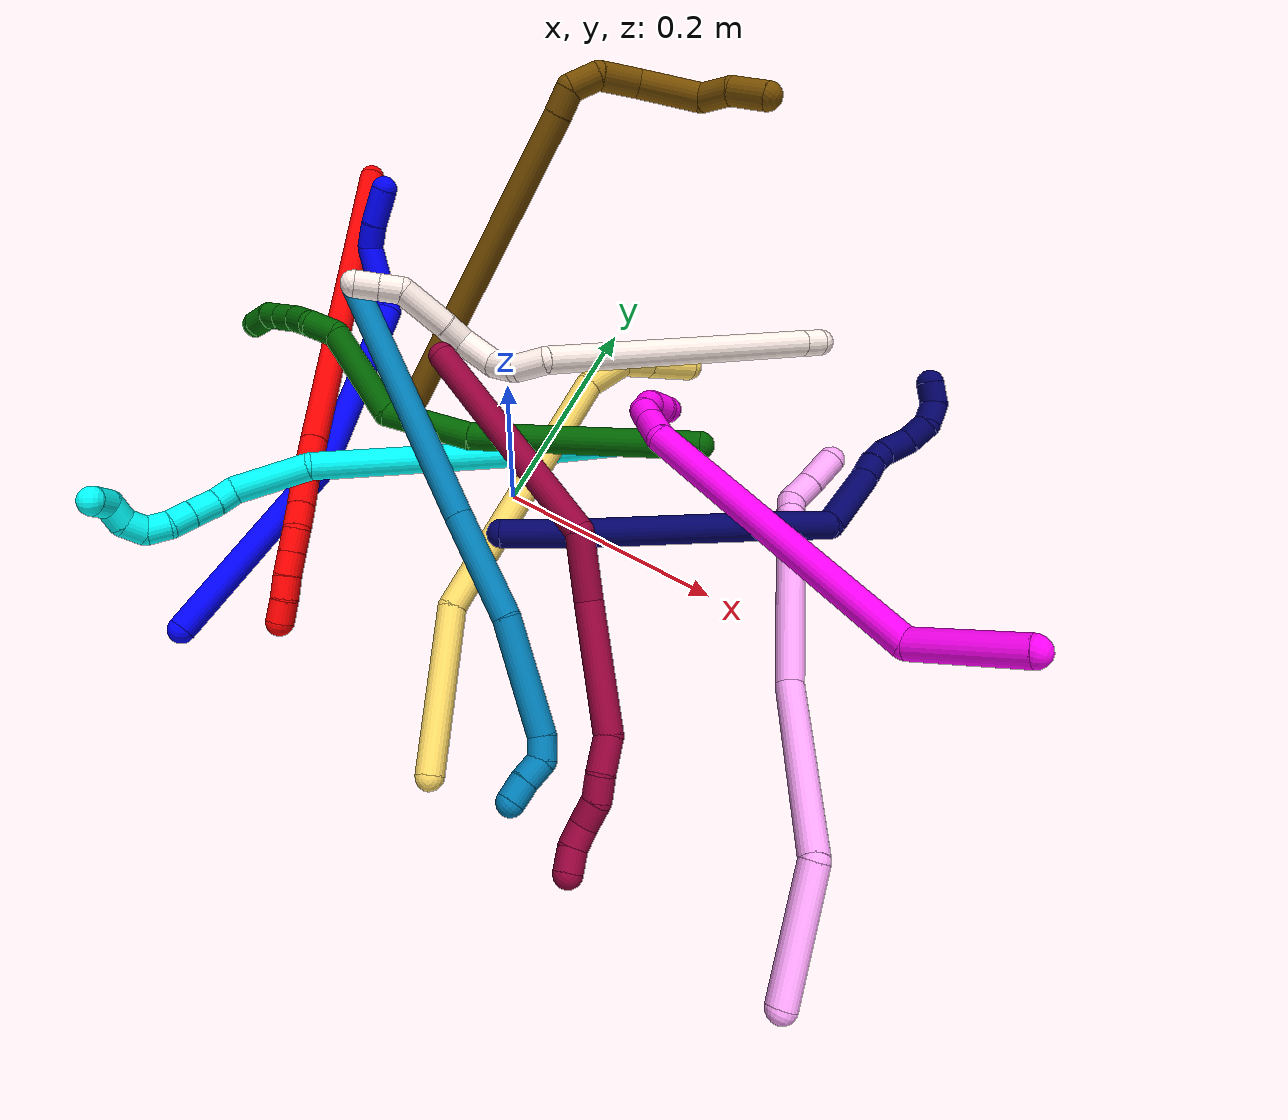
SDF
<sdf version="1.7">
 <world name="default">
  <plugin name="TubeGeneratorPlugin" filename="libtube_generator_plugin.so"/>
  <model name="photoneo_s_sensor">
   <static>1</static>
   <pose>0 0 2 1.57079 1.57079 3.14159</pose>
   <link name="link">
    <inertial><mass>0.1</mass></inertial>
    <sensor name="sensor" type="depth">
     <update_rate>30</update_rate>
     <camera>
      <horizontal_fov>1.22</horizontal_fov>
      <image><width>1920</width><height>1200</height><format>B8G8R8</format></image>
      <clip><near>0.1</near><far>4</far></clip>
      <depth_camera><output>points</output></depth_camera>
     </camera>
     <plugin name="camera_plugin" filename="libgazebo_ros_depth_camera.so">
      <baseline>0.2</baseline>
      <alwaysOn>1</alwaysOn>
      <updateRate>0.0</updateRate>
      <cameraName>camera_ir</cameraName>
      <imageTopicName>/camera/color/image_raw</imageTopicName>
      <cameraInfoTopicName>/camera/color/camera_info</cameraInfoTopicName>
      <depthImageTopicName>/camera/depth/image_raw</depthImageTopicName>
      <depthImageCameraInfoTopicName>/camera/depth/camera_info</depthImageCameraInfoTopicName>
      <pointCloudTopicName>/camera/depth/points</pointCloudTopicName>
      <frameName>fr_optical</frameName>
      <pointCloudCutoff>0.1</pointCloudCutoff>
      <pointCloudCutoffMax>2.0</pointCloudCutoffMax>
      <distortionK1>0</distortionK1>
      <distortionK2>0</distortionK2>
      <distortionK3>0</distortionK3>
      <distortionT1>0</distortionT1>
      <distortionT2>0</distortionT2>
      <CxPrime>0</CxPrime>
      <Cx>0</Cx>
      <Cy>0</Cy>
      <focalLength>0</focalLength>
      <hackBaseline>0</hackBaseline>
     </plugin>
    </sensor>
   </link>
  </model>
  <gravity>0 0 -9.8</gravity>
  <magnetic_field>6e-06 2.3e-05 -4.2e-05</magnetic_field>
  <atmosphere type="adiabatic"/>
  <physics name="default_physics" default="0" type="ode">
   <max_step_size>0.003</max_step_size>
   <real_time_factor>1</real_time_factor>
   <real_time_update_rate>1000</real_time_update_rate>
   <max_contacts>10000</max_contacts>
   <ode>
    <solver>
     <type>quick</type>
     <iters>100</iters>
     <sor>1.3</sor>
     <use_dynamic_moi_rescaling>0</use_dynamic_moi_rescaling>
    </solver>
    <constraints>
     <contact_max_correcting_vel>0</contact_max_correcting_vel>
     <contact_surface_layer>0.001</contact_surface_layer>
     <cfm>0</cfm>
     <erp>0.2</erp>
    </constraints>
   </ode>
  </physics>
  <scene><ambient>0.4 0.4 0.4 1</ambient><background>0.7 0.7 0.7 1</background><shadows>0</shadows></scene>
  <audio><device>default</device></audio>
  <spherical_coordinates>
   <surface_model>EARTH_WGS84</surface_model>
   <latitude_deg>0</latitude_deg>
   <longitude_deg>0</longitude_deg>
   <elevation>0</elevation>
   <heading_deg>0</heading_deg>
  </spherical_coordinates>
  <model name="bin">
   <static>1</static>
   <link name="bottom">
    <collision name="collision-bottom">
     <pose>0 0 -0.01 0 -0 0</pose>
     <geometry><box><size>0.8 0.6 0.02</size></box></geometry>
     <surface>
      <friction><ode><mu>100</mu><mu2>100</mu2></ode></friction>
      <contact><collide_bitmask>65535</collide_bitmask></contact>
     </surface>
    </collision>
   </link>
   <link name="west_wall">
    <collision name="collision-west_wall">
     <pose>-0.41 0 0.1 0 -0 0</pose>
     <geometry><box><size>0.02 0.6 0.2</size></box></geometry>
     <surface>
      <friction><ode><mu>100</mu><mu2>100</mu2></ode></friction>
      <contact><collide_bitmask>65535</collide_bitmask></contact>
     </surface>
    </collision>
   </link>
   <link name="east_wall">
    <collision name="collision-east_wall">
     <pose>0.41 0 0.1 0 -0 0</pose>
     <geometry><box><size>0.02 0.6 0.2</size></box></geometry>
     <surface>
      <friction><ode><mu>100</mu><mu2>100</mu2></ode></friction>
      <contact><collide_bitmask>65535</collide_bitmask></contact>
     </surface>
    </collision>
   </link>
   <link name="south_wall">
    <collision name="collision-south_wall">
     <pose>0 -0.31 0.1 0 -0 0</pose>
     <geometry><box><size>0.8 0.02 0.2</size></box></geometry>
     <surface>
      <friction><ode><mu>100</mu><mu2>100</mu2></ode></friction>
      <contact><collide_bitmask>65535</collide_bitmask></contact>
     </surface>
    </collision>
   </link>
   <link name="north_wall">
    <collision name="collision-north_wall">
     <pose>0 0.31 0.1 0 -0 0</pose>
     <geometry><box><size>0.8 0.02 0.2</size></box></geometry>
     <surface>
      <friction><ode><mu>100</mu><mu2>100</mu2></ode></friction>
      <contact><collide_bitmask>65535</collide_bitmask></contact>
     </surface>
    </collision>
   </link>
  </model>
  <model name="1">
   <static>0</static>
   <link name="1">
    <collision name="collision-cylinder-e_1_1_4">
     <pose>0.001475 0.088067 -0.039302 -1.99055 0.015292 -0.02357</pose>
     <geometry><cylinder><radius>0.0125</radius><length>0.192901</length></cylinder></geometry>
     <surface>
      <friction><ode><mu>1.16</mu><mu2>1.16</mu2><slip1>0</slip1><slip2>0</slip2></ode></friction>
      <contact><ode><kp>1e+06</kp><kd>1</kd><max_vel>0</max_vel><min_depth>0.001</min_depth></ode></contact>
     </surface>
    </collision>
    <visual name="visual-cylinder-e_1_1_4">
     <pose>0.001475 0.088067 -0.039302 -1.99055 0.015292 -0.02357</pose>
     <geometry><cylinder><radius>0.0125</radius><length>0.192901</length></cylinder></geometry>
     <material><ambient>0 0 1 1</ambient></material>
    </visual>
    <collision name="collision-cylinder-e_2_4_5">
     <pose>0.03096 0.249667 -0.116082 -2.04216 0.327187 -0.526315</pose>
     <geometry><cylinder><radius>0.0125</radius><length>0.174312</length></cylinder></geometry>
     <surface>
      <friction><ode><mu>1.16</mu><mu2>1.16</mu2><slip1>0</slip1><slip2>0</slip2></ode></friction>
      <contact><ode><kp>1e+06</kp><kd>1</kd><max_vel>0</max_vel><min_depth>0.001</min_depth></ode></contact>
     </surface>
    </collision>
    <visual name="visual-cylinder-e_2_4_5">
     <pose>0.03096 0.249667 -0.116082 -2.04216 0.327187 -0.526315</pose>
     <geometry><cylinder><radius>0.0125</radius><length>0.174312</length></cylinder></geometry>
     <material><ambient>0 0 1 1</ambient></material>
    </visual>
    <collision name="collision-cylinder-e_3_5_6">
     <pose>0.06734 0.330035 -0.153644 -1.58298 0.885909 -0.895384</pose>
     <geometry><cylinder><radius>0.0125</radius><length>0.021614</length></cylinder></geometry>
     <surface>
      <friction><ode><mu>1.16</mu><mu2>1.16</mu2><slip1>0</slip1><slip2>0</slip2></ode></friction>
      <contact><ode><kp>1e+06</kp><kd>1</kd><max_vel>0</max_vel><min_depth>0.001</min_depth></ode></contact>
     </surface>
    </collision>
    <visual name="visual-cylinder-e_3_5_6">
     <pose>0.06734 0.330035 -0.153644 -1.58298 0.885909 -0.895384</pose>
     <geometry><cylinder><radius>0.0125</radius><length>0.021614</length></cylinder></geometry>
     <material><ambient>0 0 1 1</ambient></material>
    </visual>
    <collision name="collision-cylinder-e_4_6_7">
     <pose>0.093678 0.344658 -0.17084 -2.71455 0.762741 -2.15022</pose>
     <geometry><cylinder><radius>0.0125</radius><length>0.052014</length></cylinder></geometry>
     <surface>
      <friction><ode><mu>1.16</mu><mu2>1.16</mu2><slip1>0</slip1><slip2>0</slip2></ode></friction>
      <contact><ode><kp>1e+06</kp><kd>1</kd><max_vel>0</max_vel><min_depth>0.001</min_depth></ode></contact>
     </surface>
    </collision>
    <visual name="visual-cylinder-e_4_6_7">
     <pose>0.093678 0.344658 -0.17084 -2.71455 0.762741 -2.15022</pose>
     <geometry><cylinder><radius>0.0125</radius><length>0.052014</length></cylinder></geometry>
     <material><ambient>0 0 1 1</ambient></material>
    </visual>
    <collision name="collision-cylinder-e_5_7_8">
     <pose>0.113622 0.355694 -0.199212 -2.86069 0.166996 -1.06896</pose>
     <geometry><cylinder><radius>0.0125</radius><length>0.023768</length></cylinder></geometry>
     <surface>
      <friction><ode><mu>1.16</mu><mu2>1.16</mu2><slip1>0</slip1><slip2>0</slip2></ode></friction>
      <contact><ode><kp>1e+06</kp><kd>1</kd><max_vel>0</max_vel><min_depth>0.001</min_depth></ode></contact>
     </surface>
    </collision>
    <visual name="visual-cylinder-e_5_7_8">
     <pose>0.113622 0.355694 -0.199212 -2.86069 0.166996 -1.06896</pose>
     <geometry><cylinder><radius>0.0125</radius><length>0.023768</length></cylinder></geometry>
     <material><ambient>0 0 1 1</ambient></material>
    </visual>
    <collision name="collision-cylinder-e_6_8_2">
     <pose>0.11736 0.365966 -0.226618 -2.73131 0.09979 -0.471095</pose>
     <geometry><cylinder><radius>0.0125</radius><length>0.035392</length></cylinder></geometry>
     <surface>
      <friction><ode><mu>1.16</mu><mu2>1.16</mu2><slip1>0</slip1><slip2>0</slip2></ode></friction>
      <contact><ode><kp>1e+06</kp><kd>1</kd><max_vel>0</max_vel><min_depth>0.001</min_depth></ode></contact>
     </surface>
    </collision>
    <visual name="visual-cylinder-e_6_8_2">
     <pose>0.11736 0.365966 -0.226618 -2.73131 0.09979 -0.471095</pose>
     <geometry><cylinder><radius>0.0125</radius><length>0.035392</length></cylinder></geometry>
     <material><ambient>0 0 1 1</ambient></material>
    </visual>
    <collision name="collision-sphere-2">
     <pose>0.119123 0.372989 -0.242765 0 -0 0</pose>
     <geometry><sphere><radius>0.0125</radius></sphere></geometry>
     <surface>
      <friction><ode><mu>1.16</mu><mu2>1.16</mu2><slip1>0</slip1><slip2>0</slip2></ode></friction>
      <contact><ode><kp>1e+06</kp><kd>1</kd><max_vel>0</max_vel><min_depth>0.001</min_depth></ode></contact>
     </surface>
    </collision>
    <visual name="visual-sphere-2">
     <pose>0.119123 0.372989 -0.242765 0 -0 0</pose>
     <geometry><sphere><radius>0.0125</radius></sphere></geometry>
     <material><ambient>0 0 1 1</ambient></material>
    </visual>
    <collision name="collision-sphere-4">
     <pose>0.00295 0.176135 -0.078604 0 -0 0</pose>
     <geometry><sphere><radius>0.0125</radius></sphere></geometry>
     <surface>
      <friction><ode><mu>1.16</mu><mu2>1.16</mu2><slip1>0</slip1><slip2>0</slip2></ode></friction>
      <contact><ode><kp>1e+06</kp><kd>1</kd><max_vel>0</max_vel><min_depth>0.001</min_depth></ode></contact>
     </surface>
    </collision>
    <visual name="visual-sphere-4">
     <pose>0.00295 0.176135 -0.078604 0 -0 0</pose>
     <geometry><sphere><radius>0.0125</radius></sphere></geometry>
     <material><ambient>0 0 1 1</ambient></material>
    </visual>
    <collision name="collision-sphere-1">
     <geometry><sphere><radius>0.0125</radius></sphere></geometry>
     <surface>
      <friction><ode><mu>1.16</mu><mu2>1.16</mu2><slip1>0</slip1><slip2>0</slip2></ode></friction>
      <contact><ode><kp>1e+06</kp><kd>1</kd><max_vel>0</max_vel><min_depth>0.001</min_depth></ode></contact>
     </surface>
    </collision>
    <visual name="visual-sphere-1">
     <geometry><sphere><radius>0.0125</radius></sphere></geometry>
     <material><ambient>0 0 1 1</ambient></material>
    </visual>
    <collision name="collision-sphere-8">
     <pose>0.115597 0.358943 -0.210472 0 -0 0</pose>
     <geometry><sphere><radius>0.0125</radius></sphere></geometry>
     <surface>
      <friction><ode><mu>1.16</mu><mu2>1.16</mu2><slip1>0</slip1><slip2>0</slip2></ode></friction>
      <contact><ode><kp>1e+06</kp><kd>1</kd><max_vel>0</max_vel><min_depth>0.001</min_depth></ode></contact>
     </surface>
    </collision>
    <visual name="visual-sphere-8">
     <pose>0.115597 0.358943 -0.210472 0 -0 0</pose>
     <geometry><sphere><radius>0.0125</radius></sphere></geometry>
     <material><ambient>0 0 1 1</ambient></material>
    </visual>
    <collision name="collision-sphere-5">
     <pose>0.05897 0.323199 -0.153561 0 -0 0</pose>
     <geometry><sphere><radius>0.0125</radius></sphere></geometry>
     <surface>
      <friction><ode><mu>1.16</mu><mu2>1.16</mu2><slip1>0</slip1><slip2>0</slip2></ode></friction>
      <contact><ode><kp>1e+06</kp><kd>1</kd><max_vel>0</max_vel><min_depth>0.001</min_depth></ode></contact>
     </surface>
    </collision>
    <visual name="visual-sphere-5">
     <pose>0.05897 0.323199 -0.153561 0 -0 0</pose>
     <geometry><sphere><radius>0.0125</radius></sphere></geometry>
     <material><ambient>0 0 1 1</ambient></material>
    </visual>
    <collision name="collision-sphere-6">
     <pose>0.07571 0.336871 -0.153727 0 -0 0</pose>
     <geometry><sphere><radius>0.0125</radius></sphere></geometry>
     <surface>
      <friction><ode><mu>1.16</mu><mu2>1.16</mu2><slip1>0</slip1><slip2>0</slip2></ode></friction>
      <contact><ode><kp>1e+06</kp><kd>1</kd><max_vel>0</max_vel><min_depth>0.001</min_depth></ode></contact>
     </surface>
    </collision>
    <visual name="visual-sphere-6">
     <pose>0.07571 0.336871 -0.153727 0 -0 0</pose>
     <geometry><sphere><radius>0.0125</radius></sphere></geometry>
     <material><ambient>0 0 1 1</ambient></material>
    </visual>
    <collision name="collision-sphere-7">
     <pose>0.111646 0.352445 -0.187953 0 -0 0</pose>
     <geometry><sphere><radius>0.0125</radius></sphere></geometry>
     <surface>
      <friction><ode><mu>1.16</mu><mu2>1.16</mu2><slip1>0</slip1><slip2>0</slip2></ode></friction>
      <contact><ode><kp>1e+06</kp><kd>1</kd><max_vel>0</max_vel><min_depth>0.001</min_depth></ode></contact>
     </surface>
    </collision>
    <visual name="visual-sphere-7">
     <pose>0.111646 0.352445 -0.187953 0 -0 0</pose>
     <geometry><sphere><radius>0.0125</radius></sphere></geometry>
     <material><ambient>0 0 1 1</ambient></material>
    </visual>
    <inertial>
     <pose>0.037727 0.213949 -0.105556 0 -0 0</pose>
     <mass>0.5</mass>
     <inertia>
      <ixx>0.000742</ixx>
      <ixy>0</ixy>
      <ixz>0</ixz>
      <iyy>-0.000563</iyy>
      <iyz>0</iyz>
      <izz>-0.001123</izz>
     </inertia>
    </inertial>
   </link>
   <pose>-0.184654 -0.255955 0.011626 -2.72166 0.033668 3.02924</pose>
  </model>
  <model name="2">
   <static>0</static>
   <link name="2">
    <collision name="collision-cylinder-e_1_1_4">
     <pose>0.129001 -0.098259 -0.023393 1.80452 0.906522 1.10516</pose>
     <geometry><cylinder><radius>0.0125</radius><length>0.327679</length></cylinder></geometry>
     <surface>
      <friction><ode><mu>1.16</mu><mu2>1.16</mu2><slip1>0</slip1><slip2>0</slip2></ode></friction>
      <contact><ode><kp>1e+06</kp><kd>1</kd><max_vel>0</max_vel><min_depth>0.001</min_depth></ode></contact>
     </surface>
    </collision>
    <visual name="visual-cylinder-e_1_1_4">
     <pose>0.129001 -0.098259 -0.023393 1.80452 0.906522 1.10516</pose>
     <geometry><cylinder><radius>0.0125</radius><length>0.327679</length></cylinder></geometry>
     <material><ambient>1 0 0 1</ambient></material>
    </visual>
    <collision name="collision-cylinder-e_2_4_5">
     <pose>0.275159 -0.20929 -0.049686 1.79404 0.918792 1.10941</pose>
     <geometry><cylinder><radius>0.0125</radius><length>0.043169</length></cylinder></geometry>
     <surface>
      <friction><ode><mu>1.16</mu><mu2>1.16</mu2><slip1>0</slip1><slip2>0</slip2></ode></friction>
      <contact><ode><kp>1e+06</kp><kd>1</kd><max_vel>0</max_vel><min_depth>0.001</min_depth></ode></contact>
     </surface>
    </collision>
    <visual name="visual-cylinder-e_2_4_5">
     <pose>0.275159 -0.20929 -0.049686 1.79404 0.918792 1.10941</pose>
     <geometry><cylinder><radius>0.0125</radius><length>0.043169</length></cylinder></geometry>
     <material><ambient>1 0 0 1</ambient></material>
    </visual>
    <collision name="collision-cylinder-e_3_5_6">
     <pose>0.302155 -0.229583 -0.05383 1.73476 0.911549 1.04811</pose>
     <geometry><cylinder><radius>0.0125</radius><length>0.024894</length></cylinder></geometry>
     <surface>
      <friction><ode><mu>1.16</mu><mu2>1.16</mu2><slip1>0</slip1><slip2>0</slip2></ode></friction>
      <contact><ode><kp>1e+06</kp><kd>1</kd><max_vel>0</max_vel><min_depth>0.001</min_depth></ode></contact>
     </surface>
    </collision>
    <visual name="visual-cylinder-e_3_5_6">
     <pose>0.302155 -0.229583 -0.05383 1.73476 0.911549 1.04811</pose>
     <geometry><cylinder><radius>0.0125</radius><length>0.024894</length></cylinder></geometry>
     <material><ambient>1 0 0 1</ambient></material>
    </visual>
    <collision name="collision-cylinder-e_4_6_7">
     <pose>0.320652 -0.244052 -0.056391 1.75817 0.88602 1.04047</pose>
     <geometry><cylinder><radius>0.0125</radius><length>0.022357</length></cylinder></geometry>
     <surface>
      <friction><ode><mu>1.16</mu><mu2>1.16</mu2><slip1>0</slip1><slip2>0</slip2></ode></friction>
      <contact><ode><kp>1e+06</kp><kd>1</kd><max_vel>0</max_vel><min_depth>0.001</min_depth></ode></contact>
     </surface>
    </collision>
    <visual name="visual-cylinder-e_4_6_7">
     <pose>0.320652 -0.244052 -0.056391 1.75817 0.88602 1.04047</pose>
     <geometry><cylinder><radius>0.0125</radius><length>0.022357</length></cylinder></geometry>
     <material><ambient>1 0 0 1</ambient></material>
    </visual>
    <collision name="collision-cylinder-e_5_7_8">
     <pose>0.339159 -0.254278 -0.058471 1.79922 1.24141 1.46592</pose>
     <geometry><cylinder><radius>0.0125</radius><length>0.020816</length></cylinder></geometry>
     <surface>
      <friction><ode><mu>1.16</mu><mu2>1.16</mu2><slip1>0</slip1><slip2>0</slip2></ode></friction>
      <contact><ode><kp>1e+06</kp><kd>1</kd><max_vel>0</max_vel><min_depth>0.001</min_depth></ode></contact>
     </surface>
    </collision>
    <visual name="visual-cylinder-e_5_7_8">
     <pose>0.339159 -0.254278 -0.058471 1.79922 1.24141 1.46592</pose>
     <geometry><cylinder><radius>0.0125</radius><length>0.020816</length></cylinder></geometry>
     <material><ambient>1 0 0 1</ambient></material>
    </visual>
    <collision name="collision-cylinder-e_6_8_9">
     <pose>0.358862 -0.260855 -0.060003 1.80019 1.23979 1.4652</pose>
     <geometry><cylinder><radius>0.0125</radius><length>0.02084</length></cylinder></geometry>
     <surface>
      <friction><ode><mu>1.16</mu><mu2>1.16</mu2><slip1>0</slip1><slip2>0</slip2></ode></friction>
      <contact><ode><kp>1e+06</kp><kd>1</kd><max_vel>0</max_vel><min_depth>0.001</min_depth></ode></contact>
     </surface>
    </collision>
    <visual name="visual-cylinder-e_6_8_9">
     <pose>0.358862 -0.260855 -0.060003 1.80019 1.23979 1.4652</pose>
     <geometry><cylinder><radius>0.0125</radius><length>0.02084</length></cylinder></geometry>
     <material><ambient>1 0 0 1</ambient></material>
    </visual>
    <collision name="collision-cylinder-e_7_9_10">
     <pose>0.378453 -0.266883 -0.060639 1.52185 1.29703 1.25022</pose>
     <geometry><cylinder><radius>0.0125</radius><length>0.020226</length></cylinder></geometry>
     <surface>
      <friction><ode><mu>1.16</mu><mu2>1.16</mu2><slip1>0</slip1><slip2>0</slip2></ode></friction>
      <contact><ode><kp>1e+06</kp><kd>1</kd><max_vel>0</max_vel><min_depth>0.001</min_depth></ode></contact>
     </surface>
    </collision>
    <visual name="visual-cylinder-e_7_9_10">
     <pose>0.378453 -0.266883 -0.060639 1.52185 1.29703 1.25022</pose>
     <geometry><cylinder><radius>0.0125</radius><length>0.020226</length></cylinder></geometry>
     <material><ambient>1 0 0 1</ambient></material>
    </visual>
    <collision name="collision-cylinder-e_8_10_2">
     <pose>0.398127 -0.27078 -0.060778 1.80035 1.45092 1.682</pose>
     <geometry><cylinder><radius>0.0125</radius><length>0.020019</length></cylinder></geometry>
     <surface>
      <friction><ode><mu>1.16</mu><mu2>1.16</mu2><slip1>0</slip1><slip2>0</slip2></ode></friction>
      <contact><ode><kp>1e+06</kp><kd>1</kd><max_vel>0</max_vel><min_depth>0.001</min_depth></ode></contact>
     </surface>
    </collision>
    <visual name="visual-cylinder-e_8_10_2">
     <pose>0.398127 -0.27078 -0.060778 1.80035 1.45092 1.682</pose>
     <geometry><cylinder><radius>0.0125</radius><length>0.020019</length></cylinder></geometry>
     <material><ambient>1 0 0 1</ambient></material>
    </visual>
    <collision name="collision-sphere-2">
     <pose>0.408065 -0.271945 -0.06105 0 -0 0</pose>
     <geometry><sphere><radius>0.0125</radius></sphere></geometry>
     <surface>
      <friction><ode><mu>1.16</mu><mu2>1.16</mu2><slip1>0</slip1><slip2>0</slip2></ode></friction>
      <contact><ode><kp>1e+06</kp><kd>1</kd><max_vel>0</max_vel><min_depth>0.001</min_depth></ode></contact>
     </surface>
    </collision>
    <visual name="visual-sphere-2">
     <pose>0.408065 -0.271945 -0.06105 0 -0 0</pose>
     <geometry><sphere><radius>0.0125</radius></sphere></geometry>
     <material><ambient>1 0 0 1</ambient></material>
    </visual>
    <collision name="collision-sphere-10">
     <pose>0.388189 -0.269614 -0.060506 0 -0 0</pose>
     <geometry><sphere><radius>0.0125</radius></sphere></geometry>
     <surface>
      <friction><ode><mu>1.16</mu><mu2>1.16</mu2><slip1>0</slip1><slip2>0</slip2></ode></friction>
      <contact><ode><kp>1e+06</kp><kd>1</kd><max_vel>0</max_vel><min_depth>0.001</min_depth></ode></contact>
     </surface>
    </collision>
    <visual name="visual-sphere-10">
     <pose>0.388189 -0.269614 -0.060506 0 -0 0</pose>
     <geometry><sphere><radius>0.0125</radius></sphere></geometry>
     <material><ambient>1 0 0 1</ambient></material>
    </visual>
    <collision name="collision-sphere-9">
     <pose>0.368716 -0.264152 -0.060773 0 -0 0</pose>
     <geometry><sphere><radius>0.0125</radius></sphere></geometry>
     <surface>
      <friction><ode><mu>1.16</mu><mu2>1.16</mu2><slip1>0</slip1><slip2>0</slip2></ode></friction>
      <contact><ode><kp>1e+06</kp><kd>1</kd><max_vel>0</max_vel><min_depth>0.001</min_depth></ode></contact>
     </surface>
    </collision>
    <visual name="visual-sphere-9">
     <pose>0.368716 -0.264152 -0.060773 0 -0 0</pose>
     <geometry><sphere><radius>0.0125</radius></sphere></geometry>
     <material><ambient>1 0 0 1</ambient></material>
    </visual>
    <collision name="collision-sphere-4">
     <pose>0.258003 -0.196517 -0.046786 0 -0 0</pose>
     <geometry><sphere><radius>0.0125</radius></sphere></geometry>
     <surface>
      <friction><ode><mu>1.16</mu><mu2>1.16</mu2><slip1>0</slip1><slip2>0</slip2></ode></friction>
      <contact><ode><kp>1e+06</kp><kd>1</kd><max_vel>0</max_vel><min_depth>0.001</min_depth></ode></contact>
     </surface>
    </collision>
    <visual name="visual-sphere-4">
     <pose>0.258003 -0.196517 -0.046786 0 -0 0</pose>
     <geometry><sphere><radius>0.0125</radius></sphere></geometry>
     <material><ambient>1 0 0 1</ambient></material>
    </visual>
    <collision name="collision-sphere-1">
     <geometry><sphere><radius>0.0125</radius></sphere></geometry>
     <surface>
      <friction><ode><mu>1.16</mu><mu2>1.16</mu2><slip1>0</slip1><slip2>0</slip2></ode></friction>
      <contact><ode><kp>1e+06</kp><kd>1</kd><max_vel>0</max_vel><min_depth>0.001</min_depth></ode></contact>
     </surface>
    </collision>
    <visual name="visual-sphere-1">
     <geometry><sphere><radius>0.0125</radius></sphere></geometry>
     <material><ambient>1 0 0 1</ambient></material>
    </visual>
    <collision name="collision-sphere-8">
     <pose>0.349008 -0.257557 -0.059233 0 -0 0</pose>
     <geometry><sphere><radius>0.0125</radius></sphere></geometry>
     <surface>
      <friction><ode><mu>1.16</mu><mu2>1.16</mu2><slip1>0</slip1><slip2>0</slip2></ode></friction>
      <contact><ode><kp>1e+06</kp><kd>1</kd><max_vel>0</max_vel><min_depth>0.001</min_depth></ode></contact>
     </surface>
    </collision>
    <visual name="visual-sphere-8">
     <pose>0.349008 -0.257557 -0.059233 0 -0 0</pose>
     <geometry><sphere><radius>0.0125</radius></sphere></geometry>
     <material><ambient>1 0 0 1</ambient></material>
    </visual>
    <collision name="collision-sphere-5">
     <pose>0.292316 -0.222062 -0.052585 0 -0 0</pose>
     <geometry><sphere><radius>0.0125</radius></sphere></geometry>
     <surface>
      <friction><ode><mu>1.16</mu><mu2>1.16</mu2><slip1>0</slip1><slip2>0</slip2></ode></friction>
      <contact><ode><kp>1e+06</kp><kd>1</kd><max_vel>0</max_vel><min_depth>0.001</min_depth></ode></contact>
     </surface>
    </collision>
    <visual name="visual-sphere-5">
     <pose>0.292316 -0.222062 -0.052585 0 -0 0</pose>
     <geometry><sphere><radius>0.0125</radius></sphere></geometry>
     <material><ambient>1 0 0 1</ambient></material>
    </visual>
    <collision name="collision-sphere-6">
     <pose>0.311994 -0.237105 -0.055074 0 -0 0</pose>
     <geometry><sphere><radius>0.0125</radius></sphere></geometry>
     <surface>
      <friction><ode><mu>1.16</mu><mu2>1.16</mu2><slip1>0</slip1><slip2>0</slip2></ode></friction>
      <contact><ode><kp>1e+06</kp><kd>1</kd><max_vel>0</max_vel><min_depth>0.001</min_depth></ode></contact>
     </surface>
    </collision>
    <visual name="visual-sphere-6">
     <pose>0.311994 -0.237105 -0.055074 0 -0 0</pose>
     <geometry><sphere><radius>0.0125</radius></sphere></geometry>
     <material><ambient>1 0 0 1</ambient></material>
    </visual>
    <collision name="collision-sphere-7">
     <pose>0.329311 -0.250999 -0.057708 0 -0 0</pose>
     <geometry><sphere><radius>0.0125</radius></sphere></geometry>
     <surface>
      <friction><ode><mu>1.16</mu><mu2>1.16</mu2><slip1>0</slip1><slip2>0</slip2></ode></friction>
      <contact><ode><kp>1e+06</kp><kd>1</kd><max_vel>0</max_vel><min_depth>0.001</min_depth></ode></contact>
     </surface>
    </collision>
    <visual name="visual-sphere-7">
     <pose>0.329311 -0.250999 -0.057708 0 -0 0</pose>
     <geometry><sphere><radius>0.0125</radius></sphere></geometry>
     <material><ambient>1 0 0 1</ambient></material>
    </visual>
    <inertial>
     <pose>0.198007 -0.147903 -0.034644 0 -0 0</pose>
     <mass>0.5</mass>
     <inertia>
      <ixx>0.002481</ixx>
      <ixy>0</ixy>
      <ixz>0</ixz>
      <iyy>0.003331</iyy>
      <iyz>0</iyz>
      <izz>-0.000564</izz>
     </inertia>
    </inertial>
   </link>
   <pose>-0.312466 0.243422 0.012019 -2.08499 0.576401 -1.32056</pose>
  </model>
  <model name="3">
   <static>0</static>
   <link name="3">
    <collision name="collision-cylinder-e_1_1_4">
     <pose>-0.003328 -0.001134 0.047422 0.023901 -0.070034 -0.000837</pose>
     <geometry><cylinder><radius>0.0125</radius><length>0.095104</length></cylinder></geometry>
     <surface>
      <friction><ode><mu>1.16</mu><mu2>1.16</mu2><slip1>0</slip1><slip2>0</slip2></ode></friction>
      <contact><ode><kp>1e+06</kp><kd>1</kd><max_vel>0</max_vel><min_depth>0.001</min_depth></ode></contact>
     </surface>
    </collision>
    <visual name="visual-cylinder-e_1_1_4">
     <pose>-0.003328 -0.001134 0.047422 0.023901 -0.070034 -0.000837</pose>
     <geometry><cylinder><radius>0.0125</radius><length>0.095104</length></cylinder></geometry>
     <material><ambient>0.003922 1 0.996078 1</ambient></material>
    </visual>
    <collision name="collision-cylinder-e_2_4_5">
     <pose>-0.007986 -0.018782 0.18823 0.175034 -0.01403 -0.001231</pose>
     <geometry><cylinder><radius>0.0125</radius><length>0.18969</length></cylinder></geometry>
     <surface>
      <friction><ode><mu>1.16</mu><mu2>1.16</mu2><slip1>0</slip1><slip2>0</slip2></ode></friction>
      <contact><ode><kp>1e+06</kp><kd>1</kd><max_vel>0</max_vel><min_depth>0.001</min_depth></ode></contact>
     </surface>
    </collision>
    <visual name="visual-cylinder-e_2_4_5">
     <pose>-0.007986 -0.018782 0.18823 0.175034 -0.01403 -0.001231</pose>
     <geometry><cylinder><radius>0.0125</radius><length>0.18969</length></cylinder></geometry>
     <material><ambient>0.003922 1 0.996078 1</ambient></material>
    </visual>
    <collision name="collision-cylinder-e_3_5_6">
     <pose>-0.019521 -0.030261 0.315017 -0.149641 -0.293396 0.022151</pose>
     <geometry><cylinder><radius>0.0125</radius><length>0.070571</length></cylinder></geometry>
     <surface>
      <friction><ode><mu>1.16</mu><mu2>1.16</mu2><slip1>0</slip1><slip2>0</slip2></ode></friction>
      <contact><ode><kp>1e+06</kp><kd>1</kd><max_vel>0</max_vel><min_depth>0.001</min_depth></ode></contact>
     </surface>
    </collision>
    <visual name="visual-cylinder-e_3_5_6">
     <pose>-0.019521 -0.030261 0.315017 -0.149641 -0.293396 0.022151</pose>
     <geometry><cylinder><radius>0.0125</radius><length>0.070571</length></cylinder></geometry>
     <material><ambient>0.003922 1 0.996078 1</ambient></material>
    </visual>
    <collision name="collision-cylinder-e_4_6_7">
     <pose>-0.034315 -0.030051 0.356074 0.562363 -0.469249 -0.137859</pose>
     <geometry><cylinder><radius>0.0125</radius><length>0.020295</length></cylinder></geometry>
     <surface>
      <friction><ode><mu>1.16</mu><mu2>1.16</mu2><slip1>0</slip1><slip2>0</slip2></ode></friction>
      <contact><ode><kp>1e+06</kp><kd>1</kd><max_vel>0</max_vel><min_depth>0.001</min_depth></ode></contact>
     </surface>
    </collision>
    <visual name="visual-cylinder-e_4_6_7">
     <pose>-0.034315 -0.030051 0.356074 0.562363 -0.469249 -0.137859</pose>
     <geometry><cylinder><radius>0.0125</radius><length>0.020295</length></cylinder></geometry>
     <material><ambient>0.003922 1 0.996078 1</ambient></material>
    </visual>
    <collision name="collision-cylinder-e_5_7_8">
     <pose>-0.042728 -0.040797 0.373463 0.5465 -0.323889 -0.091511</pose>
     <geometry><cylinder><radius>0.0125</radius><length>0.024031</length></cylinder></geometry>
     <surface>
      <friction><ode><mu>1.16</mu><mu2>1.16</mu2><slip1>0</slip1><slip2>0</slip2></ode></friction>
      <contact><ode><kp>1e+06</kp><kd>1</kd><max_vel>0</max_vel><min_depth>0.001</min_depth></ode></contact>
     </surface>
    </collision>
    <visual name="visual-cylinder-e_5_7_8">
     <pose>-0.042728 -0.040797 0.373463 0.5465 -0.323889 -0.091511</pose>
     <geometry><cylinder><radius>0.0125</radius><length>0.024031</length></cylinder></geometry>
     <material><ambient>0.003922 1 0.996078 1</ambient></material>
    </visual>
    <collision name="collision-cylinder-e_6_8_9">
     <pose>-0.049945 -0.051797 0.39122 0.564357 -0.343127 -0.100381</pose>
     <geometry><cylinder><radius>0.0125</radius><length>0.020173</length></cylinder></geometry>
     <surface>
      <friction><ode><mu>1.16</mu><mu2>1.16</mu2><slip1>0</slip1><slip2>0</slip2></ode></friction>
      <contact><ode><kp>1e+06</kp><kd>1</kd><max_vel>0</max_vel><min_depth>0.001</min_depth></ode></contact>
     </surface>
    </collision>
    <visual name="visual-cylinder-e_6_8_9">
     <pose>-0.049945 -0.051797 0.39122 0.564357 -0.343127 -0.100381</pose>
     <geometry><cylinder><radius>0.0125</radius><length>0.020173</length></cylinder></geometry>
     <material><ambient>0.003922 1 0.996078 1</ambient></material>
    </visual>
    <collision name="collision-cylinder-e_7_9_10">
     <pose>-0.055128 -0.059688 0.408723 0.288277 -0.179048 -0.026056</pose>
     <geometry><cylinder><radius>0.0125</radius><length>0.020093</length></cylinder></geometry>
     <surface>
      <friction><ode><mu>1.16</mu><mu2>1.16</mu2><slip1>0</slip1><slip2>0</slip2></ode></friction>
      <contact><ode><kp>1e+06</kp><kd>1</kd><max_vel>0</max_vel><min_depth>0.001</min_depth></ode></contact>
     </surface>
    </collision>
    <visual name="visual-cylinder-e_7_9_10">
     <pose>-0.055128 -0.059688 0.408723 0.288277 -0.179048 -0.026056</pose>
     <geometry><cylinder><radius>0.0125</radius><length>0.020093</length></cylinder></geometry>
     <material><ambient>0.003922 1 0.996078 1</ambient></material>
    </visual>
    <collision name="collision-cylinder-e_8_10_11">
     <pose>-0.052347 -0.06625 0.426272 0.435087 0.47433 0.106756</pose>
     <geometry><cylinder><radius>0.0125</radius><length>0.020009</length></cylinder></geometry>
     <surface>
      <friction><ode><mu>1.16</mu><mu2>1.16</mu2><slip1>0</slip1><slip2>0</slip2></ode></friction>
      <contact><ode><kp>1e+06</kp><kd>1</kd><max_vel>0</max_vel><min_depth>0.001</min_depth></ode></contact>
     </surface>
    </collision>
    <visual name="visual-cylinder-e_8_10_11">
     <pose>-0.052347 -0.06625 0.426272 0.435087 0.47433 0.106756</pose>
     <geometry><cylinder><radius>0.0125</radius><length>0.020009</length></cylinder></geometry>
     <material><ambient>0.003922 1 0.996078 1</ambient></material>
    </visual>
    <collision name="collision-cylinder-e_9_11_12">
     <pose>-0.039464 -0.073395 0.438759 0.65523 0.98061 0.35892</pose>
     <geometry><cylinder><radius>0.0125</radius><length>0.020014</length></cylinder></geometry>
     <surface>
      <friction><ode><mu>1.16</mu><mu2>1.16</mu2><slip1>0</slip1><slip2>0</slip2></ode></friction>
      <contact><ode><kp>1e+06</kp><kd>1</kd><max_vel>0</max_vel><min_depth>0.001</min_depth></ode></contact>
     </surface>
    </collision>
    <visual name="visual-cylinder-e_9_11_12">
     <pose>-0.039464 -0.073395 0.438759 0.65523 0.98061 0.35892</pose>
     <geometry><cylinder><radius>0.0125</radius><length>0.020014</length></cylinder></geometry>
     <material><ambient>0.003922 1 0.996078 1</ambient></material>
    </visual>
    <collision name="collision-cylinder-e_10_12_2">
     <pose>-0.028296 -0.085407 0.44739 1.11592 0.289062 0.181176</pose>
     <geometry><cylinder><radius>0.0125</radius><length>0.02002</length></cylinder></geometry>
     <surface>
      <friction><ode><mu>1.16</mu><mu2>1.16</mu2><slip1>0</slip1><slip2>0</slip2></ode></friction>
      <contact><ode><kp>1e+06</kp><kd>1</kd><max_vel>0</max_vel><min_depth>0.001</min_depth></ode></contact>
     </surface>
    </collision>
    <visual name="visual-cylinder-e_10_12_2">
     <pose>-0.028296 -0.085407 0.44739 1.11592 0.289062 0.181176</pose>
     <geometry><cylinder><radius>0.0125</radius><length>0.02002</length></cylinder></geometry>
     <material><ambient>0.003922 1 0.996078 1</ambient></material>
    </visual>
    <collision name="collision-sphere-2">
     <pose>-0.025443 -0.094026 0.451606 0 -0 0</pose>
     <geometry><sphere><radius>0.0125</radius></sphere></geometry>
     <surface>
      <friction><ode><mu>1.16</mu><mu2>1.16</mu2><slip1>0</slip1><slip2>0</slip2></ode></friction>
      <contact><ode><kp>1e+06</kp><kd>1</kd><max_vel>0</max_vel><min_depth>0.001</min_depth></ode></contact>
     </surface>
    </collision>
    <visual name="visual-sphere-2">
     <pose>-0.025443 -0.094026 0.451606 0 -0 0</pose>
     <geometry><sphere><radius>0.0125</radius></sphere></geometry>
     <material><ambient>0.003922 1 0.996078 1</ambient></material>
    </visual>
    <collision name="collision-sphere-12">
     <pose>-0.031149 -0.076788 0.443175 0 -0 0</pose>
     <geometry><sphere><radius>0.0125</radius></sphere></geometry>
     <surface>
      <friction><ode><mu>1.16</mu><mu2>1.16</mu2><slip1>0</slip1><slip2>0</slip2></ode></friction>
      <contact><ode><kp>1e+06</kp><kd>1</kd><max_vel>0</max_vel><min_depth>0.001</min_depth></ode></contact>
     </surface>
    </collision>
    <visual name="visual-sphere-12">
     <pose>-0.031149 -0.076788 0.443175 0 -0 0</pose>
     <geometry><sphere><radius>0.0125</radius></sphere></geometry>
     <material><ambient>0.003922 1 0.996078 1</ambient></material>
    </visual>
    <collision name="collision-sphere-11">
     <pose>-0.047778 -0.070001 0.434343 0 -0 0</pose>
     <geometry><sphere><radius>0.0125</radius></sphere></geometry>
     <surface>
      <friction><ode><mu>1.16</mu><mu2>1.16</mu2><slip1>0</slip1><slip2>0</slip2></ode></friction>
      <contact><ode><kp>1e+06</kp><kd>1</kd><max_vel>0</max_vel><min_depth>0.001</min_depth></ode></contact>
     </surface>
    </collision>
    <visual name="visual-sphere-11">
     <pose>-0.047778 -0.070001 0.434343 0 -0 0</pose>
     <geometry><sphere><radius>0.0125</radius></sphere></geometry>
     <material><ambient>0.003922 1 0.996078 1</ambient></material>
    </visual>
    <collision name="collision-sphere-10">
     <pose>-0.056917 -0.062498 0.418201 0 -0 0</pose>
     <geometry><sphere><radius>0.0125</radius></sphere></geometry>
     <surface>
      <friction><ode><mu>1.16</mu><mu2>1.16</mu2><slip1>0</slip1><slip2>0</slip2></ode></friction>
      <contact><ode><kp>1e+06</kp><kd>1</kd><max_vel>0</max_vel><min_depth>0.001</min_depth></ode></contact>
     </surface>
    </collision>
    <visual name="visual-sphere-10">
     <pose>-0.056917 -0.062498 0.418201 0 -0 0</pose>
     <geometry><sphere><radius>0.0125</radius></sphere></geometry>
     <material><ambient>0.003922 1 0.996078 1</ambient></material>
    </visual>
    <collision name="collision-sphere-9">
     <pose>-0.053338 -0.056877 0.399246 0 -0 0</pose>
     <geometry><sphere><radius>0.0125</radius></sphere></geometry>
     <surface>
      <friction><ode><mu>1.16</mu><mu2>1.16</mu2><slip1>0</slip1><slip2>0</slip2></ode></friction>
      <contact><ode><kp>1e+06</kp><kd>1</kd><max_vel>0</max_vel><min_depth>0.001</min_depth></ode></contact>
     </surface>
    </collision>
    <visual name="visual-sphere-9">
     <pose>-0.053338 -0.056877 0.399246 0 -0 0</pose>
     <geometry><sphere><radius>0.0125</radius></sphere></geometry>
     <material><ambient>0.003922 1 0.996078 1</ambient></material>
    </visual>
    <collision name="collision-sphere-4">
     <pose>-0.006655 -0.002267 0.094843 0 -0 0</pose>
     <geometry><sphere><radius>0.0125</radius></sphere></geometry>
     <surface>
      <friction><ode><mu>1.16</mu><mu2>1.16</mu2><slip1>0</slip1><slip2>0</slip2></ode></friction>
      <contact><ode><kp>1e+06</kp><kd>1</kd><max_vel>0</max_vel><min_depth>0.001</min_depth></ode></contact>
     </surface>
    </collision>
    <visual name="visual-sphere-4">
     <pose>-0.006655 -0.002267 0.094843 0 -0 0</pose>
     <geometry><sphere><radius>0.0125</radius></sphere></geometry>
     <material><ambient>0.003922 1 0.996078 1</ambient></material>
    </visual>
    <collision name="collision-sphere-1">
     <geometry><sphere><radius>0.0125</radius></sphere></geometry>
     <surface>
      <friction><ode><mu>1.16</mu><mu2>1.16</mu2><slip1>0</slip1><slip2>0</slip2></ode></friction>
      <contact><ode><kp>1e+06</kp><kd>1</kd><max_vel>0</max_vel><min_depth>0.001</min_depth></ode></contact>
     </surface>
    </collision>
    <visual name="visual-sphere-1">
     <geometry><sphere><radius>0.0125</radius></sphere></geometry>
     <material><ambient>0.003922 1 0.996078 1</ambient></material>
    </visual>
    <collision name="collision-sphere-8">
     <pose>-0.046552 -0.046717 0.383195 0 -0 0</pose>
     <geometry><sphere><radius>0.0125</radius></sphere></geometry>
     <surface>
      <friction><ode><mu>1.16</mu><mu2>1.16</mu2><slip1>0</slip1><slip2>0</slip2></ode></friction>
      <contact><ode><kp>1e+06</kp><kd>1</kd><max_vel>0</max_vel><min_depth>0.001</min_depth></ode></contact>
     </surface>
    </collision>
    <visual name="visual-sphere-8">
     <pose>-0.046552 -0.046717 0.383195 0 -0 0</pose>
     <geometry><sphere><radius>0.0125</radius></sphere></geometry>
     <material><ambient>0.003922 1 0.996078 1</ambient></material>
    </visual>
    <collision name="collision-sphere-5">
     <pose>-0.009316 -0.035297 0.281617 0 -0 0</pose>
     <geometry><sphere><radius>0.0125</radius></sphere></geometry>
     <surface>
      <friction><ode><mu>1.16</mu><mu2>1.16</mu2><slip1>0</slip1><slip2>0</slip2></ode></friction>
      <contact><ode><kp>1e+06</kp><kd>1</kd><max_vel>0</max_vel><min_depth>0.001</min_depth></ode></contact>
     </surface>
    </collision>
    <visual name="visual-sphere-5">
     <pose>-0.009316 -0.035297 0.281617 0 -0 0</pose>
     <geometry><sphere><radius>0.0125</radius></sphere></geometry>
     <material><ambient>0.003922 1 0.996078 1</ambient></material>
    </visual>
    <collision name="collision-sphere-6">
     <pose>-0.029726 -0.025226 0.348418 0 -0 0</pose>
     <geometry><sphere><radius>0.0125</radius></sphere></geometry>
     <surface>
      <friction><ode><mu>1.16</mu><mu2>1.16</mu2><slip1>0</slip1><slip2>0</slip2></ode></friction>
      <contact><ode><kp>1e+06</kp><kd>1</kd><max_vel>0</max_vel><min_depth>0.001</min_depth></ode></contact>
     </surface>
    </collision>
    <visual name="visual-sphere-6">
     <pose>-0.029726 -0.025226 0.348418 0 -0 0</pose>
     <geometry><sphere><radius>0.0125</radius></sphere></geometry>
     <material><ambient>0.003922 1 0.996078 1</ambient></material>
    </visual>
    <collision name="collision-sphere-7">
     <pose>-0.038904 -0.034877 0.363731 0 -0 0</pose>
     <geometry><sphere><radius>0.0125</radius></sphere></geometry>
     <surface>
      <friction><ode><mu>1.16</mu><mu2>1.16</mu2><slip1>0</slip1><slip2>0</slip2></ode></friction>
      <contact><ode><kp>1e+06</kp><kd>1</kd><max_vel>0</max_vel><min_depth>0.001</min_depth></ode></contact>
     </surface>
    </collision>
    <visual name="visual-sphere-7">
     <pose>-0.038904 -0.034877 0.363731 0 -0 0</pose>
     <geometry><sphere><radius>0.0125</radius></sphere></geometry>
     <material><ambient>0.003922 1 0.996078 1</ambient></material>
    </visual>
    <inertial>
     <pose>-0.018902 -0.02829 0.242039 0 -0 0</pose>
     <mass>0.5</mass>
     <inertia><ixx>0.00069</ixx><ixy>0</ixy><ixz>0</ixz><iyy>0.000676</iyy><iyz>0</iyz><izz>0.00016</izz></inertia>
    </inertial>
   </link>
   <pose>0.060456 0.091188 0.011448 -1.45426 -0.587532 2.09978</pose>
  </model>
  <model name="4">
   <static>0</static>
   <link name="4">
    <collision name="collision-cylinder-e_1_1_4">
     <pose>-0.001423 0.008335 -0.052731 -2.98482 -0.026646 0.336054</pose>
     <geometry><cylinder><radius>0.0125</radius><length>0.106808</length></cylinder></geometry>
     <surface>
      <friction><ode><mu>1.16</mu><mu2>1.16</mu2><slip1>0</slip1><slip2>0</slip2></ode></friction>
      <contact><ode><kp>1e+06</kp><kd>1</kd><max_vel>0</max_vel><min_depth>0.001</min_depth></ode></contact>
     </surface>
    </collision>
    <visual name="visual-cylinder-e_1_1_4">
     <pose>-0.001423 0.008335 -0.052731 -2.98482 -0.026646 0.336054</pose>
     <geometry><cylinder><radius>0.0125</radius><length>0.106808</length></cylinder></geometry>
     <material><ambient>1 0.65098 0.996078 1</ambient></material>
    </visual>
    <collision name="collision-cylinder-e_2_4_5">
     <pose>-0.051087 0.044701 -0.165305 -2.70354 -0.630576 1.94387</pose>
     <geometry><cylinder><radius>0.0125</radius><length>0.163636</length></cylinder></geometry>
     <surface>
      <friction><ode><mu>1.16</mu><mu2>1.16</mu2><slip1>0</slip1><slip2>0</slip2></ode></friction>
      <contact><ode><kp>1e+06</kp><kd>1</kd><max_vel>0</max_vel><min_depth>0.001</min_depth></ode></contact>
     </surface>
    </collision>
    <visual name="visual-cylinder-e_2_4_5">
     <pose>-0.051087 0.044701 -0.165305 -2.70354 -0.630576 1.94387</pose>
     <geometry><cylinder><radius>0.0125</radius><length>0.163636</length></cylinder></geometry>
     <material><ambient>1 0.65098 0.996078 1</ambient></material>
    </visual>
    <collision name="collision-cylinder-e_3_5_6">
     <pose>-0.106267 0.099853 -0.294885 -2.77069 -0.092484 0.483662</pose>
     <geometry><cylinder><radius>0.0125</radius><length>0.150291</length></cylinder></geometry>
     <surface>
      <friction><ode><mu>1.16</mu><mu2>1.16</mu2><slip1>0</slip1><slip2>0</slip2></ode></friction>
      <contact><ode><kp>1e+06</kp><kd>1</kd><max_vel>0</max_vel><min_depth>0.001</min_depth></ode></contact>
     </surface>
    </collision>
    <visual name="visual-cylinder-e_3_5_6">
     <pose>-0.106267 0.099853 -0.294885 -2.77069 -0.092484 0.483662</pose>
     <geometry><cylinder><radius>0.0125</radius><length>0.150291</length></cylinder></geometry>
     <material><ambient>1 0.65098 0.996078 1</ambient></material>
    </visual>
    <collision name="collision-cylinder-e_4_6_7">
     <pose>-0.120642 0.128691 -0.371654 -2.90221 -0.798731 2.58638</pose>
     <geometry><cylinder><radius>0.0125</radius><length>0.020754</length></cylinder></geometry>
     <surface>
      <friction><ode><mu>1.16</mu><mu2>1.16</mu2><slip1>0</slip1><slip2>0</slip2></ode></friction>
      <contact><ode><kp>1e+06</kp><kd>1</kd><max_vel>0</max_vel><min_depth>0.001</min_depth></ode></contact>
     </surface>
    </collision>
    <visual name="visual-cylinder-e_4_6_7">
     <pose>-0.120642 0.128691 -0.371654 -2.90221 -0.798731 2.58638</pose>
     <geometry><cylinder><radius>0.0125</radius><length>0.020754</length></cylinder></geometry>
     <material><ambient>1 0.65098 0.996078 1</ambient></material>
    </visual>
    <collision name="collision-cylinder-e_5_7_8">
     <pose>-0.131044 0.125826 -0.390494 2.77147 -0.230172 -1.10636</pose>
     <geometry><cylinder><radius>0.0125</radius><length>0.026015</length></cylinder></geometry>
     <surface>
      <friction><ode><mu>1.16</mu><mu2>1.16</mu2><slip1>0</slip1><slip2>0</slip2></ode></friction>
      <contact><ode><kp>1e+06</kp><kd>1</kd><max_vel>0</max_vel><min_depth>0.001</min_depth></ode></contact>
     </surface>
    </collision>
    <visual name="visual-cylinder-e_5_7_8">
     <pose>-0.131044 0.125826 -0.390494 2.77147 -0.230172 -1.10636</pose>
     <geometry><cylinder><radius>0.0125</radius><length>0.026015</length></cylinder></geometry>
     <material><ambient>1 0.65098 0.996078 1</ambient></material>
    </visual>
    <collision name="collision-cylinder-e_6_8_2">
     <pose>-0.138209 0.116524 -0.41727 2.83609 -0.261322 -1.41313</pose>
     <geometry><cylinder><radius>0.0125</radius><length>0.032495</length></cylinder></geometry>
     <surface>
      <friction><ode><mu>1.16</mu><mu2>1.16</mu2><slip1>0</slip1><slip2>0</slip2></ode></friction>
      <contact><ode><kp>1e+06</kp><kd>1</kd><max_vel>0</max_vel><min_depth>0.001</min_depth></ode></contact>
     </surface>
    </collision>
    <visual name="visual-cylinder-e_6_8_2">
     <pose>-0.138209 0.116524 -0.41727 2.83609 -0.261322 -1.41313</pose>
     <geometry><cylinder><radius>0.0125</radius><length>0.032495</length></cylinder></geometry>
     <material><ambient>1 0.65098 0.996078 1</ambient></material>
    </visual>
    <collision name="collision-sphere-2">
     <pose>-0.142407 0.111803 -0.432239 0 -0 0</pose>
     <geometry><sphere><radius>0.0125</radius></sphere></geometry>
     <surface>
      <friction><ode><mu>1.16</mu><mu2>1.16</mu2><slip1>0</slip1><slip2>0</slip2></ode></friction>
      <contact><ode><kp>1e+06</kp><kd>1</kd><max_vel>0</max_vel><min_depth>0.001</min_depth></ode></contact>
     </surface>
    </collision>
    <visual name="visual-sphere-2">
     <pose>-0.142407 0.111803 -0.432239 0 -0 0</pose>
     <geometry><sphere><radius>0.0125</radius></sphere></geometry>
     <material><ambient>1 0.65098 0.996078 1</ambient></material>
    </visual>
    <collision name="collision-sphere-4">
     <pose>-0.002846 0.01667 -0.105461 0 -0 0</pose>
     <geometry><sphere><radius>0.0125</radius></sphere></geometry>
     <surface>
      <friction><ode><mu>1.16</mu><mu2>1.16</mu2><slip1>0</slip1><slip2>0</slip2></ode></friction>
      <contact><ode><kp>1e+06</kp><kd>1</kd><max_vel>0</max_vel><min_depth>0.001</min_depth></ode></contact>
     </surface>
    </collision>
    <visual name="visual-sphere-4">
     <pose>-0.002846 0.01667 -0.105461 0 -0 0</pose>
     <geometry><sphere><radius>0.0125</radius></sphere></geometry>
     <material><ambient>1 0.65098 0.996078 1</ambient></material>
    </visual>
    <collision name="collision-sphere-1">
     <geometry><sphere><radius>0.0125</radius></sphere></geometry>
     <surface>
      <friction><ode><mu>1.16</mu><mu2>1.16</mu2><slip1>0</slip1><slip2>0</slip2></ode></friction>
      <contact><ode><kp>1e+06</kp><kd>1</kd><max_vel>0</max_vel><min_depth>0.001</min_depth></ode></contact>
     </surface>
    </collision>
    <visual name="visual-sphere-1">
     <geometry><sphere><radius>0.0125</radius></sphere></geometry>
     <material><ambient>1 0.65098 0.996078 1</ambient></material>
    </visual>
    <collision name="collision-sphere-8">
     <pose>-0.134012 0.121245 -0.402301 0 -0 0</pose>
     <geometry><sphere><radius>0.0125</radius></sphere></geometry>
     <surface>
      <friction><ode><mu>1.16</mu><mu2>1.16</mu2><slip1>0</slip1><slip2>0</slip2></ode></friction>
      <contact><ode><kp>1e+06</kp><kd>1</kd><max_vel>0</max_vel><min_depth>0.001</min_depth></ode></contact>
     </surface>
    </collision>
    <visual name="visual-sphere-8">
     <pose>-0.134012 0.121245 -0.402301 0 -0 0</pose>
     <geometry><sphere><radius>0.0125</radius></sphere></geometry>
     <material><ambient>1 0.65098 0.996078 1</ambient></material>
    </visual>
    <collision name="collision-sphere-5">
     <pose>-0.099327 0.072733 -0.225149 0 -0 0</pose>
     <geometry><sphere><radius>0.0125</radius></sphere></geometry>
     <surface>
      <friction><ode><mu>1.16</mu><mu2>1.16</mu2><slip1>0</slip1><slip2>0</slip2></ode></friction>
      <contact><ode><kp>1e+06</kp><kd>1</kd><max_vel>0</max_vel><min_depth>0.001</min_depth></ode></contact>
     </surface>
    </collision>
    <visual name="visual-sphere-5">
     <pose>-0.099327 0.072733 -0.225149 0 -0 0</pose>
     <geometry><sphere><radius>0.0125</radius></sphere></geometry>
     <material><ambient>1 0.65098 0.996078 1</ambient></material>
    </visual>
    <collision name="collision-sphere-6">
     <pose>-0.113207 0.126974 -0.364622 0 -0 0</pose>
     <geometry><sphere><radius>0.0125</radius></sphere></geometry>
     <surface>
      <friction><ode><mu>1.16</mu><mu2>1.16</mu2><slip1>0</slip1><slip2>0</slip2></ode></friction>
      <contact><ode><kp>1e+06</kp><kd>1</kd><max_vel>0</max_vel><min_depth>0.001</min_depth></ode></contact>
     </surface>
    </collision>
    <visual name="visual-sphere-6">
     <pose>-0.113207 0.126974 -0.364622 0 -0 0</pose>
     <geometry><sphere><radius>0.0125</radius></sphere></geometry>
     <material><ambient>1 0.65098 0.996078 1</ambient></material>
    </visual>
    <collision name="collision-sphere-7">
     <pose>-0.128076 0.130407 -0.378687 0 -0 0</pose>
     <geometry><sphere><radius>0.0125</radius></sphere></geometry>
     <surface>
      <friction><ode><mu>1.16</mu><mu2>1.16</mu2><slip1>0</slip1><slip2>0</slip2></ode></friction>
      <contact><ode><kp>1e+06</kp><kd>1</kd><max_vel>0</max_vel><min_depth>0.001</min_depth></ode></contact>
     </surface>
    </collision>
    <visual name="visual-sphere-7">
     <pose>-0.128076 0.130407 -0.378687 0 -0 0</pose>
     <geometry><sphere><radius>0.0125</radius></sphere></geometry>
     <material><ambient>1 0.65098 0.996078 1</ambient></material>
    </visual>
    <inertial>
     <pose>-0.069773 0.065886 -0.216864 0 -0 0</pose>
     <mass>0.5</mass>
     <inertia>
      <ixx>0.000677</ixx>
      <ixy>0</ixy>
      <ixz>0</ixz>
      <iyy>0.000328</iyy>
      <iyz>0</iyz>
      <izz>-2.9e-05</izz>
     </inertia>
    </inertial>
   </link>
   <pose>0.387897 -0.2795 0.047532 3.03464 -1.30917 -1.39101</pose>
  </model>
  <model name="5">
   <static>0</static>
   <link name="5">
    <collision name="collision-cylinder-e_1_1_4">
     <pose>-0.036842 0.055721 -0.025047 -1.99324 -0.54267 0.812296</pose>
     <geometry><cylinder><radius>0.0125</radius><length>0.142681</length></cylinder></geometry>
     <surface>
      <friction><ode><mu>1.16</mu><mu2>1.16</mu2><slip1>0</slip1><slip2>0</slip2></ode></friction>
      <contact><ode><kp>1e+06</kp><kd>1</kd><max_vel>0</max_vel><min_depth>0.001</min_depth></ode></contact>
     </surface>
    </collision>
    <visual name="visual-cylinder-e_1_1_4">
     <pose>-0.036842 0.055721 -0.025047 -1.99324 -0.54267 0.812296</pose>
     <geometry><cylinder><radius>0.0125</radius><length>0.142681</length></cylinder></geometry>
     <material><ambient>1 0.858824 0.4 1</ambient></material>
    </visual>
    <collision name="collision-cylinder-e_2_4_5">
     <pose>-0.089916 0.225487 -0.092026 -1.92313 -0.132799 0.190024</pose>
     <geometry><cylinder><radius>0.0125</radius><length>0.24518</length></cylinder></geometry>
     <surface>
      <friction><ode><mu>1.16</mu><mu2>1.16</mu2><slip1>0</slip1><slip2>0</slip2></ode></friction>
      <contact><ode><kp>1e+06</kp><kd>1</kd><max_vel>0</max_vel><min_depth>0.001</min_depth></ode></contact>
     </surface>
    </collision>
    <visual name="visual-cylinder-e_2_4_5">
     <pose>-0.089916 0.225487 -0.092026 -1.92313 -0.132799 0.190024</pose>
     <geometry><cylinder><radius>0.0125</radius><length>0.24518</length></cylinder></geometry>
     <material><ambient>1 0.858824 0.4 1</ambient></material>
    </visual>
    <collision name="collision-cylinder-e_3_5_6">
     <pose>-0.100296 0.357277 -0.135761 -1.67203 0.317019 -0.3502</pose>
     <geometry><cylinder><radius>0.0125</radius><length>0.037541</length></cylinder></geometry>
     <surface>
      <friction><ode><mu>1.16</mu><mu2>1.16</mu2><slip1>0</slip1><slip2>0</slip2></ode></friction>
      <contact><ode><kp>1e+06</kp><kd>1</kd><max_vel>0</max_vel><min_depth>0.001</min_depth></ode></contact>
     </surface>
    </collision>
    <visual name="visual-cylinder-e_3_5_6">
     <pose>-0.100296 0.357277 -0.135761 -1.67203 0.317019 -0.3502</pose>
     <geometry><cylinder><radius>0.0125</radius><length>0.037541</length></cylinder></geometry>
     <material><ambient>1 0.858824 0.4 1</ambient></material>
    </visual>
    <collision name="collision-cylinder-e_4_6_7">
     <pose>-0.084944 0.38258 -0.144538 -2.31606 0.74578 -1.45818</pose>
     <geometry><cylinder><radius>0.0125</radius><length>0.028004</length></cylinder></geometry>
     <surface>
      <friction><ode><mu>1.16</mu><mu2>1.16</mu2><slip1>0</slip1><slip2>0</slip2></ode></friction>
      <contact><ode><kp>1e+06</kp><kd>1</kd><max_vel>0</max_vel><min_depth>0.001</min_depth></ode></contact>
     </surface>
    </collision>
    <visual name="visual-cylinder-e_4_6_7">
     <pose>-0.084944 0.38258 -0.144538 -2.31606 0.74578 -1.45818</pose>
     <geometry><cylinder><radius>0.0125</radius><length>0.028004</length></cylinder></geometry>
     <material><ambient>1 0.858824 0.4 1</ambient></material>
    </visual>
    <collision name="collision-cylinder-e_5_7_2">
     <pose>-0.059698 0.402694 -0.163227 -2.32156 0.742114 -1.46026</pose>
     <geometry><cylinder><radius>0.0125</radius><length>0.046594</length></cylinder></geometry>
     <surface>
      <friction><ode><mu>1.16</mu><mu2>1.16</mu2><slip1>0</slip1><slip2>0</slip2></ode></friction>
      <contact><ode><kp>1e+06</kp><kd>1</kd><max_vel>0</max_vel><min_depth>0.001</min_depth></ode></contact>
     </surface>
    </collision>
    <visual name="visual-cylinder-e_5_7_2">
     <pose>-0.059698 0.402694 -0.163227 -2.32156 0.742114 -1.46026</pose>
     <geometry><cylinder><radius>0.0125</radius><length>0.046594</length></cylinder></geometry>
     <material><ambient>1 0.858824 0.4 1</ambient></material>
    </visual>
    <collision name="collision-sphere-2">
     <pose>-0.043952 0.415248 -0.174941 0 -0 0</pose>
     <geometry><sphere><radius>0.0125</radius></sphere></geometry>
     <surface>
      <friction><ode><mu>1.16</mu><mu2>1.16</mu2><slip1>0</slip1><slip2>0</slip2></ode></friction>
      <contact><ode><kp>1e+06</kp><kd>1</kd><max_vel>0</max_vel><min_depth>0.001</min_depth></ode></contact>
     </surface>
    </collision>
    <visual name="visual-sphere-2">
     <pose>-0.043952 0.415248 -0.174941 0 -0 0</pose>
     <geometry><sphere><radius>0.0125</radius></sphere></geometry>
     <material><ambient>1 0.858824 0.4 1</ambient></material>
    </visual>
    <collision name="collision-sphere-7">
     <pose>-0.075443 0.390139 -0.151514 0 -0 0</pose>
     <geometry><sphere><radius>0.0125</radius></sphere></geometry>
     <surface>
      <friction><ode><mu>1.16</mu><mu2>1.16</mu2><slip1>0</slip1><slip2>0</slip2></ode></friction>
      <contact><ode><kp>1e+06</kp><kd>1</kd><max_vel>0</max_vel><min_depth>0.001</min_depth></ode></contact>
     </surface>
    </collision>
    <visual name="visual-sphere-7">
     <pose>-0.075443 0.390139 -0.151514 0 -0 0</pose>
     <geometry><sphere><radius>0.0125</radius></sphere></geometry>
     <material><ambient>1 0.858824 0.4 1</ambient></material>
    </visual>
    <collision name="collision-sphere-6">
     <pose>-0.094445 0.375021 -0.137563 0 -0 0</pose>
     <geometry><sphere><radius>0.0125</radius></sphere></geometry>
     <surface>
      <friction><ode><mu>1.16</mu><mu2>1.16</mu2><slip1>0</slip1><slip2>0</slip2></ode></friction>
      <contact><ode><kp>1e+06</kp><kd>1</kd><max_vel>0</max_vel><min_depth>0.001</min_depth></ode></contact>
     </surface>
    </collision>
    <visual name="visual-sphere-6">
     <pose>-0.094445 0.375021 -0.137563 0 -0 0</pose>
     <geometry><sphere><radius>0.0125</radius></sphere></geometry>
     <material><ambient>1 0.858824 0.4 1</ambient></material>
    </visual>
    <collision name="collision-sphere-5">
     <pose>-0.106148 0.339533 -0.133958 0 -0 0</pose>
     <geometry><sphere><radius>0.0125</radius></sphere></geometry>
     <surface>
      <friction><ode><mu>1.16</mu><mu2>1.16</mu2><slip1>0</slip1><slip2>0</slip2></ode></friction>
      <contact><ode><kp>1e+06</kp><kd>1</kd><max_vel>0</max_vel><min_depth>0.001</min_depth></ode></contact>
     </surface>
    </collision>
    <visual name="visual-sphere-5">
     <pose>-0.106148 0.339533 -0.133958 0 -0 0</pose>
     <geometry><sphere><radius>0.0125</radius></sphere></geometry>
     <material><ambient>1 0.858824 0.4 1</ambient></material>
    </visual>
    <collision name="collision-sphere-1">
     <geometry><sphere><radius>0.0125</radius></sphere></geometry>
     <surface>
      <friction><ode><mu>1.16</mu><mu2>1.16</mu2><slip1>0</slip1><slip2>0</slip2></ode></friction>
      <contact><ode><kp>1e+06</kp><kd>1</kd><max_vel>0</max_vel><min_depth>0.001</min_depth></ode></contact>
     </surface>
    </collision>
    <visual name="visual-sphere-1">
     <geometry><sphere><radius>0.0125</radius></sphere></geometry>
     <material><ambient>1 0.858824 0.4 1</ambient></material>
    </visual>
    <collision name="collision-sphere-4">
     <pose>-0.073684 0.111441 -0.050093 0 -0 0</pose>
     <geometry><sphere><radius>0.0125</radius></sphere></geometry>
     <surface>
      <friction><ode><mu>1.16</mu><mu2>1.16</mu2><slip1>0</slip1><slip2>0</slip2></ode></friction>
      <contact><ode><kp>1e+06</kp><kd>1</kd><max_vel>0</max_vel><min_depth>0.001</min_depth></ode></contact>
     </surface>
    </collision>
    <visual name="visual-sphere-4">
     <pose>-0.073684 0.111441 -0.050093 0 -0 0</pose>
     <geometry><sphere><radius>0.0125</radius></sphere></geometry>
     <material><ambient>1 0.858824 0.4 1</ambient></material>
    </visual>
    <inertial>
     <pose>-0.072456 0.212249 -0.085772 0 -0 0</pose>
     <mass>0.5</mass>
     <inertia>
      <ixx>0.001728</ixx>
      <ixy>0</ixy>
      <ixz>0</ixz>
      <iyy>3.7e-05</iyy>
      <iyz>0</iyz>
      <izz>-0.00109</izz>
     </inertia>
    </inertial>
   </link>
   <pose>0.069591 -0.258113 0.011493 0.385021 0.284384 -0.124448</pose>
  </model>
  <model name="6">
   <static>0</static>
   <link name="6">
    <collision name="collision-cylinder-e_1_1_4">
     <pose>-0.093093 0.041727 -0.010607 -1.81973 -1.1376 1.37616</pose>
     <geometry><cylinder><radius>0.0125</radius><length>0.205134</length></cylinder></geometry>
     <surface>
      <friction><ode><mu>1.16</mu><mu2>1.16</mu2><slip1>0</slip1><slip2>0</slip2></ode></friction>
      <contact><ode><kp>1e+06</kp><kd>1</kd><max_vel>0</max_vel><min_depth>0.001</min_depth></ode></contact>
     </surface>
    </collision>
    <visual name="visual-cylinder-e_1_1_4">
     <pose>-0.093093 0.041727 -0.010607 -1.81973 -1.1376 1.37616</pose>
     <geometry><cylinder><radius>0.0125</radius><length>0.205134</length></cylinder></geometry>
     <material><ambient>0 0.392157 0.003922 1</ambient></material>
    </visual>
    <collision name="collision-cylinder-e_2_4_5">
     <pose>-0.223904 0.097382 -0.016633 -1.25301 -1.20006 0.919589</pose>
     <geometry><cylinder><radius>0.0125</radius><length>0.080935</length></cylinder></geometry>
     <surface>
      <friction><ode><mu>1.16</mu><mu2>1.16</mu2><slip1>0</slip1><slip2>0</slip2></ode></friction>
      <contact><ode><kp>1e+06</kp><kd>1</kd><max_vel>0</max_vel><min_depth>0.001</min_depth></ode></contact>
     </surface>
    </collision>
    <visual name="visual-cylinder-e_2_4_5">
     <pose>-0.223904 0.097382 -0.016633 -1.25301 -1.20006 0.919589</pose>
     <geometry><cylinder><radius>0.0125</radius><length>0.080935</length></cylinder></geometry>
     <material><ambient>0 0.392157 0.003922 1</ambient></material>
    </visual>
    <collision name="collision-cylinder-e_3_5_6">
     <pose>-0.292623 0.115995 0.019526 -0.147292 -0.77075 0.059841</pose>
     <geometry><cylinder><radius>0.0125</radius><length>0.088998</length></cylinder></geometry>
     <surface>
      <friction><ode><mu>1.16</mu><mu2>1.16</mu2><slip1>0</slip1><slip2>0</slip2></ode></friction>
      <contact><ode><kp>1e+06</kp><kd>1</kd><max_vel>0</max_vel><min_depth>0.001</min_depth></ode></contact>
     </surface>
    </collision>
    <visual name="visual-cylinder-e_3_5_6">
     <pose>-0.292623 0.115995 0.019526 -0.147292 -0.77075 0.059841</pose>
     <geometry><cylinder><radius>0.0125</radius><length>0.088998</length></cylinder></geometry>
     <material><ambient>0 0.392157 0.003922 1</ambient></material>
    </visual>
    <collision name="collision-cylinder-e_4_6_7">
     <pose>-0.336335 0.126754 0.054902 -1.01185 -1.05751 0.626086</pose>
     <geometry><cylinder><radius>0.0125</radius><length>0.029181</length></cylinder></geometry>
     <surface>
      <friction><ode><mu>1.16</mu><mu2>1.16</mu2><slip1>0</slip1><slip2>0</slip2></ode></friction>
      <contact><ode><kp>1e+06</kp><kd>1</kd><max_vel>0</max_vel><min_depth>0.001</min_depth></ode></contact>
     </surface>
    </collision>
    <visual name="visual-cylinder-e_4_6_7">
     <pose>-0.336335 0.126754 0.054902 -1.01185 -1.05751 0.626086</pose>
     <geometry><cylinder><radius>0.0125</radius><length>0.029181</length></cylinder></geometry>
     <material><ambient>0 0.392157 0.003922 1</ambient></material>
    </visual>
    <collision name="collision-cylinder-e_5_7_8">
     <pose>-0.35605 0.144874 0.063639 -1.18177 -0.493597 0.33485</pose>
     <geometry><cylinder><radius>0.0125</radius><length>0.029566</length></cylinder></geometry>
     <surface>
      <friction><ode><mu>1.16</mu><mu2>1.16</mu2><slip1>0</slip1><slip2>0</slip2></ode></friction>
      <contact><ode><kp>1e+06</kp><kd>1</kd><max_vel>0</max_vel><min_depth>0.001</min_depth></ode></contact>
     </surface>
    </collision>
    <visual name="visual-cylinder-e_5_7_8">
     <pose>-0.35605 0.144874 0.063639 -1.18177 -0.493597 0.33485</pose>
     <geometry><cylinder><radius>0.0125</radius><length>0.029566</length></cylinder></geometry>
     <material><ambient>0 0.392157 0.003922 1</ambient></material>
    </visual>
    <collision name="collision-cylinder-e_6_8_9">
     <pose>-0.370284 0.165944 0.070752 -1.33427 -0.661685 0.528384</pose>
     <geometry><cylinder><radius>0.0125</radius><length>0.023532</length></cylinder></geometry>
     <surface>
      <friction><ode><mu>1.16</mu><mu2>1.16</mu2><slip1>0</slip1><slip2>0</slip2></ode></friction>
      <contact><ode><kp>1e+06</kp><kd>1</kd><max_vel>0</max_vel><min_depth>0.001</min_depth></ode></contact>
     </surface>
    </collision>
    <visual name="visual-cylinder-e_6_8_9">
     <pose>-0.370284 0.165944 0.070752 -1.33427 -0.661685 0.528384</pose>
     <geometry><cylinder><radius>0.0125</radius><length>0.023532</length></cylinder></geometry>
     <material><ambient>0 0.392157 0.003922 1</ambient></material>
    </visual>
    <collision name="collision-cylinder-e_7_9_10">
     <pose>-0.384057 0.182507 0.074873 -1.31819 -0.698973 0.550319</pose>
     <geometry><cylinder><radius>0.0125</radius><length>0.020341</length></cylinder></geometry>
     <surface>
      <friction><ode><mu>1.16</mu><mu2>1.16</mu2><slip1>0</slip1><slip2>0</slip2></ode></friction>
      <contact><ode><kp>1e+06</kp><kd>1</kd><max_vel>0</max_vel><min_depth>0.001</min_depth></ode></contact>
     </surface>
    </collision>
    <visual name="visual-cylinder-e_7_9_10">
     <pose>-0.384057 0.182507 0.074873 -1.31819 -0.698973 0.550319</pose>
     <geometry><cylinder><radius>0.0125</radius><length>0.020341</length></cylinder></geometry>
     <material><ambient>0 0.392157 0.003922 1</ambient></material>
    </visual>
    <collision name="collision-cylinder-e_8_10_2">
     <pose>-0.396346 0.199057 0.073616 -1.91237 -0.540953 0.748648</pose>
     <geometry><cylinder><radius>0.0125</radius><length>0.022312</length></cylinder></geometry>
     <surface>
      <friction><ode><mu>1.16</mu><mu2>1.16</mu2><slip1>0</slip1><slip2>0</slip2></ode></friction>
      <contact><ode><kp>1e+06</kp><kd>1</kd><max_vel>0</max_vel><min_depth>0.001</min_depth></ode></contact>
     </surface>
    </collision>
    <visual name="visual-cylinder-e_8_10_2">
     <pose>-0.396346 0.199057 0.073616 -1.91237 -0.540953 0.748648</pose>
     <geometry><cylinder><radius>0.0125</radius><length>0.022312</length></cylinder></geometry>
     <material><ambient>0 0.392157 0.003922 1</ambient></material>
    </visual>
    <collision name="collision-sphere-2">
     <pose>-0.402091 0.208067 0.070412 0 -0 0</pose>
     <geometry><sphere><radius>0.0125</radius></sphere></geometry>
     <surface>
      <friction><ode><mu>1.16</mu><mu2>1.16</mu2><slip1>0</slip1><slip2>0</slip2></ode></friction>
      <contact><ode><kp>1e+06</kp><kd>1</kd><max_vel>0</max_vel><min_depth>0.001</min_depth></ode></contact>
     </surface>
    </collision>
    <visual name="visual-sphere-2">
     <pose>-0.402091 0.208067 0.070412 0 -0 0</pose>
     <geometry><sphere><radius>0.0125</radius></sphere></geometry>
     <material><ambient>0 0.392157 0.003922 1</ambient></material>
    </visual>
    <collision name="collision-sphere-10">
     <pose>-0.390601 0.190046 0.076819 0 -0 0</pose>
     <geometry><sphere><radius>0.0125</radius></sphere></geometry>
     <surface>
      <friction><ode><mu>1.16</mu><mu2>1.16</mu2><slip1>0</slip1><slip2>0</slip2></ode></friction>
      <contact><ode><kp>1e+06</kp><kd>1</kd><max_vel>0</max_vel><min_depth>0.001</min_depth></ode></contact>
     </surface>
    </collision>
    <visual name="visual-sphere-10">
     <pose>-0.390601 0.190046 0.076819 0 -0 0</pose>
     <geometry><sphere><radius>0.0125</radius></sphere></geometry>
     <material><ambient>0 0.392157 0.003922 1</ambient></material>
    </visual>
    <collision name="collision-sphere-9">
     <pose>-0.377513 0.174969 0.072928 0 -0 0</pose>
     <geometry><sphere><radius>0.0125</radius></sphere></geometry>
     <surface>
      <friction><ode><mu>1.16</mu><mu2>1.16</mu2><slip1>0</slip1><slip2>0</slip2></ode></friction>
      <contact><ode><kp>1e+06</kp><kd>1</kd><max_vel>0</max_vel><min_depth>0.001</min_depth></ode></contact>
     </surface>
    </collision>
    <visual name="visual-sphere-9">
     <pose>-0.377513 0.174969 0.072928 0 -0 0</pose>
     <geometry><sphere><radius>0.0125</radius></sphere></geometry>
     <material><ambient>0 0.392157 0.003922 1</ambient></material>
    </visual>
    <collision name="collision-sphere-4">
     <pose>-0.186186 0.083455 -0.021214 0 -0 0</pose>
     <geometry><sphere><radius>0.0125</radius></sphere></geometry>
     <surface>
      <friction><ode><mu>1.16</mu><mu2>1.16</mu2><slip1>0</slip1><slip2>0</slip2></ode></friction>
      <contact><ode><kp>1e+06</kp><kd>1</kd><max_vel>0</max_vel><min_depth>0.001</min_depth></ode></contact>
     </surface>
    </collision>
    <visual name="visual-sphere-4">
     <pose>-0.186186 0.083455 -0.021214 0 -0 0</pose>
     <geometry><sphere><radius>0.0125</radius></sphere></geometry>
     <material><ambient>0 0.392157 0.003922 1</ambient></material>
    </visual>
    <collision name="collision-sphere-1">
     <geometry><sphere><radius>0.0125</radius></sphere></geometry>
     <surface>
      <friction><ode><mu>1.16</mu><mu2>1.16</mu2><slip1>0</slip1><slip2>0</slip2></ode></friction>
      <contact><ode><kp>1e+06</kp><kd>1</kd><max_vel>0</max_vel><min_depth>0.001</min_depth></ode></contact>
     </surface>
    </collision>
    <visual name="visual-sphere-1">
     <geometry><sphere><radius>0.0125</radius></sphere></geometry>
     <material><ambient>0 0.392157 0.003922 1</ambient></material>
    </visual>
    <collision name="collision-sphere-8">
     <pose>-0.363054 0.15692 0.068577 0 -0 0</pose>
     <geometry><sphere><radius>0.0125</radius></sphere></geometry>
     <surface>
      <friction><ode><mu>1.16</mu><mu2>1.16</mu2><slip1>0</slip1><slip2>0</slip2></ode></friction>
      <contact><ode><kp>1e+06</kp><kd>1</kd><max_vel>0</max_vel><min_depth>0.001</min_depth></ode></contact>
     </surface>
    </collision>
    <visual name="visual-sphere-8">
     <pose>-0.363054 0.15692 0.068577 0 -0 0</pose>
     <geometry><sphere><radius>0.0125</radius></sphere></geometry>
     <material><ambient>0 0.392157 0.003922 1</ambient></material>
    </visual>
    <collision name="collision-sphere-5">
     <pose>-0.261622 0.11131 -0.012052 0 -0 0</pose>
     <geometry><sphere><radius>0.0125</radius></sphere></geometry>
     <surface>
      <friction><ode><mu>1.16</mu><mu2>1.16</mu2><slip1>0</slip1><slip2>0</slip2></ode></friction>
      <contact><ode><kp>1e+06</kp><kd>1</kd><max_vel>0</max_vel><min_depth>0.001</min_depth></ode></contact>
     </surface>
    </collision>
    <visual name="visual-sphere-5">
     <pose>-0.261622 0.11131 -0.012052 0 -0 0</pose>
     <geometry><sphere><radius>0.0125</radius></sphere></geometry>
     <material><ambient>0 0.392157 0.003922 1</ambient></material>
    </visual>
    <collision name="collision-sphere-6">
     <pose>-0.323625 0.12068 0.051103 0 -0 0</pose>
     <geometry><sphere><radius>0.0125</radius></sphere></geometry>
     <surface>
      <friction><ode><mu>1.16</mu><mu2>1.16</mu2><slip1>0</slip1><slip2>0</slip2></ode></friction>
      <contact><ode><kp>1e+06</kp><kd>1</kd><max_vel>0</max_vel><min_depth>0.001</min_depth></ode></contact>
     </surface>
    </collision>
    <visual name="visual-sphere-6">
     <pose>-0.323625 0.12068 0.051103 0 -0 0</pose>
     <geometry><sphere><radius>0.0125</radius></sphere></geometry>
     <material><ambient>0 0.392157 0.003922 1</ambient></material>
    </visual>
    <collision name="collision-sphere-7">
     <pose>-0.349046 0.132829 0.058702 0 -0 0</pose>
     <geometry><sphere><radius>0.0125</radius></sphere></geometry>
     <surface>
      <friction><ode><mu>1.16</mu><mu2>1.16</mu2><slip1>0</slip1><slip2>0</slip2></ode></friction>
      <contact><ode><kp>1e+06</kp><kd>1</kd><max_vel>0</max_vel><min_depth>0.001</min_depth></ode></contact>
     </surface>
    </collision>
    <visual name="visual-sphere-7">
     <pose>-0.349046 0.132829 0.058702 0 -0 0</pose>
     <geometry><sphere><radius>0.0125</radius></sphere></geometry>
     <material><ambient>0 0.392157 0.003922 1</ambient></material>
    </visual>
    <inertial>
     <pose>-0.217944 0.093611 0.01306 0 -0 0</pose>
     <mass>0.5</mass>
     <inertia><ixx>0.00041</ixx><ixy>0</ixy><ixz>0</ixz><iyy>0.00104</iyy><iyz>0</iyz><izz>0.000434</izz></inertia>
    </inertial>
   </link>
   <pose>0.137066 0.088907 0.082214 -1.40325 0.290992 0.356351</pose>
  </model>
  <model name="7">
   <static>0</static>
   <link name="7">
    <collision name="collision-cylinder-e_1_1_4">
     <pose>0.016104 0.006634 0.031608 -0.206884 0.462553 -0.048884</pose>
     <geometry><cylinder><radius>0.0125</radius><length>0.072177</length></cylinder></geometry>
     <surface>
      <friction><ode><mu>1.16</mu><mu2>1.16</mu2><slip1>0</slip1><slip2>0</slip2></ode></friction>
      <contact><ode><kp>1e+06</kp><kd>1</kd><max_vel>0</max_vel><min_depth>0.001</min_depth></ode></contact>
     </surface>
    </collision>
    <visual name="visual-cylinder-e_1_1_4">
     <pose>0.016104 0.006634 0.031608 -0.206884 0.462553 -0.048884</pose>
     <geometry><cylinder><radius>0.0125</radius><length>0.072177</length></cylinder></geometry>
     <material><ambient>0.003922 0 0.403922 1</ambient></material>
    </visual>
    <collision name="collision-cylinder-e_2_4_5">
     <pose>0.072212 0.035843 0.128377 -0.333509 0.525658 -0.090511</pose>
     <geometry><cylinder><radius>0.0125</radius><length>0.159449</length></cylinder></geometry>
     <surface>
      <friction><ode><mu>1.16</mu><mu2>1.16</mu2><slip1>0</slip1><slip2>0</slip2></ode></friction>
      <contact><ode><kp>1e+06</kp><kd>1</kd><max_vel>0</max_vel><min_depth>0.001</min_depth></ode></contact>
     </surface>
    </collision>
    <visual name="visual-cylinder-e_2_4_5">
     <pose>0.072212 0.035843 0.128377 -0.333509 0.525658 -0.090511</pose>
     <geometry><cylinder><radius>0.0125</radius><length>0.159449</length></cylinder></geometry>
     <material><ambient>0.003922 0 0.403922 1</ambient></material>
    </visual>
    <collision name="collision-cylinder-e_3_5_6">
     <pose>0.134265 0.07318 0.208797 -0.768801 0.804282 -0.340768</pose>
     <geometry><cylinder><radius>0.0125</radius><length>0.061217</length></cylinder></geometry>
     <surface>
      <friction><ode><mu>1.16</mu><mu2>1.16</mu2><slip1>0</slip1><slip2>0</slip2></ode></friction>
      <contact><ode><kp>1e+06</kp><kd>1</kd><max_vel>0</max_vel><min_depth>0.001</min_depth></ode></contact>
     </surface>
    </collision>
    <visual name="visual-cylinder-e_3_5_6">
     <pose>0.134265 0.07318 0.208797 -0.768801 0.804282 -0.340768</pose>
     <geometry><cylinder><radius>0.0125</radius><length>0.061217</length></cylinder></geometry>
     <material><ambient>0.003922 0 0.403922 1</ambient></material>
    </visual>
    <collision name="collision-cylinder-e_4_6_7">
     <pose>0.167167 0.121803 0.231707 -1.3486 0.30302 -0.242867</pose>
     <geometry><cylinder><radius>0.0125</radius><length>0.072745</length></cylinder></geometry>
     <surface>
      <friction><ode><mu>1.16</mu><mu2>1.16</mu2><slip1>0</slip1><slip2>0</slip2></ode></friction>
      <contact><ode><kp>1e+06</kp><kd>1</kd><max_vel>0</max_vel><min_depth>0.001</min_depth></ode></contact>
     </surface>
    </collision>
    <visual name="visual-cylinder-e_4_6_7">
     <pose>0.167167 0.121803 0.231707 -1.3486 0.30302 -0.242867</pose>
     <geometry><cylinder><radius>0.0125</radius><length>0.072745</length></cylinder></geometry>
     <material><ambient>0.003922 0 0.403922 1</ambient></material>
    </visual>
    <collision name="collision-cylinder-e_5_7_8">
     <pose>0.180284 0.166242 0.241323 -1.3871 0.207387 -0.172596</pose>
     <geometry><cylinder><radius>0.0125</radius><length>0.021987</length></cylinder></geometry>
     <surface>
      <friction><ode><mu>1.16</mu><mu2>1.16</mu2><slip1>0</slip1><slip2>0</slip2></ode></friction>
      <contact><ode><kp>1e+06</kp><kd>1</kd><max_vel>0</max_vel><min_depth>0.001</min_depth></ode></contact>
     </surface>
    </collision>
    <visual name="visual-cylinder-e_5_7_8">
     <pose>0.180284 0.166242 0.241323 -1.3871 0.207387 -0.172596</pose>
     <geometry><cylinder><radius>0.0125</radius><length>0.021987</length></cylinder></geometry>
     <material><ambient>0.003922 0 0.403922 1</ambient></material>
    </visual>
    <collision name="collision-cylinder-e_6_8_9">
     <pose>0.186079 0.185716 0.246283 -1.24608 0.359755 -0.259839</pose>
     <geometry><cylinder><radius>0.0125</radius><length>0.02006</length></cylinder></geometry>
     <surface>
      <friction><ode><mu>1.16</mu><mu2>1.16</mu2><slip1>0</slip1><slip2>0</slip2></ode></friction>
      <contact><ode><kp>1e+06</kp><kd>1</kd><max_vel>0</max_vel><min_depth>0.001</min_depth></ode></contact>
     </surface>
    </collision>
    <visual name="visual-cylinder-e_6_8_9">
     <pose>0.186079 0.185716 0.246283 -1.24608 0.359755 -0.259839</pose>
     <geometry><cylinder><radius>0.0125</radius><length>0.02006</length></cylinder></geometry>
     <material><ambient>0.003922 0 0.403922 1</ambient></material>
    </visual>
    <collision name="collision-cylinder-e_7_9_10">
     <pose>0.192867 0.202759 0.259601 -0.668026 0.242837 -0.084634</pose>
     <geometry><cylinder><radius>0.0125</radius><length>0.027093</length></cylinder></geometry>
     <surface>
      <friction><ode><mu>1.16</mu><mu2>1.16</mu2><slip1>0</slip1><slip2>0</slip2></ode></friction>
      <contact><ode><kp>1e+06</kp><kd>1</kd><max_vel>0</max_vel><min_depth>0.001</min_depth></ode></contact>
     </surface>
    </collision>
    <visual name="visual-cylinder-e_7_9_10">
     <pose>0.192867 0.202759 0.259601 -0.668026 0.242837 -0.084634</pose>
     <geometry><cylinder><radius>0.0125</radius><length>0.027093</length></cylinder></geometry>
     <material><ambient>0.003922 0 0.403922 1</ambient></material>
    </visual>
    <collision name="collision-cylinder-e_8_10_11">
     <pose>0.195656 0.21846 0.278324 -0.732509 -0.041448 0.0159</pose>
     <geometry><cylinder><radius>0.0125</radius><length>0.022616</length></cylinder></geometry>
     <surface>
      <friction><ode><mu>1.16</mu><mu2>1.16</mu2><slip1>0</slip1><slip2>0</slip2></ode></friction>
      <contact><ode><kp>1e+06</kp><kd>1</kd><max_vel>0</max_vel><min_depth>0.001</min_depth></ode></contact>
     </surface>
    </collision>
    <visual name="visual-cylinder-e_8_10_11">
     <pose>0.195656 0.21846 0.278324 -0.732509 -0.041448 0.0159</pose>
     <geometry><cylinder><radius>0.0125</radius><length>0.022616</length></cylinder></geometry>
     <material><ambient>0.003922 0 0.403922 1</ambient></material>
    </visual>
    <collision name="collision-cylinder-e_9_11_12">
     <pose>0.193657 0.236261 0.28995 -1.26574 -0.141506 0.103877</pose>
     <geometry><cylinder><radius>0.0125</radius><length>0.021699</length></cylinder></geometry>
     <surface>
      <friction><ode><mu>1.16</mu><mu2>1.16</mu2><slip1>0</slip1><slip2>0</slip2></ode></friction>
      <contact><ode><kp>1e+06</kp><kd>1</kd><max_vel>0</max_vel><min_depth>0.001</min_depth></ode></contact>
     </surface>
    </collision>
    <visual name="visual-cylinder-e_9_11_12">
     <pose>0.193657 0.236261 0.28995 -1.26574 -0.141506 0.103877</pose>
     <geometry><cylinder><radius>0.0125</radius><length>0.021699</length></cylinder></geometry>
     <material><ambient>0.003922 0 0.403922 1</ambient></material>
    </visual>
    <collision name="collision-cylinder-e_10_12_2">
     <pose>0.185488 0.254611 0.293044 -1.5871 -0.686245 0.696639</pose>
     <geometry><cylinder><radius>0.0125</radius><length>0.020956</length></cylinder></geometry>
     <surface>
      <friction><ode><mu>1.16</mu><mu2>1.16</mu2><slip1>0</slip1><slip2>0</slip2></ode></friction>
      <contact><ode><kp>1e+06</kp><kd>1</kd><max_vel>0</max_vel><min_depth>0.001</min_depth></ode></contact>
     </surface>
    </collision>
    <visual name="visual-cylinder-e_10_12_2">
     <pose>0.185488 0.254611 0.293044 -1.5871 -0.686245 0.696639</pose>
     <geometry><cylinder><radius>0.0125</radius><length>0.020956</length></cylinder></geometry>
     <material><ambient>0.003922 0 0.403922 1</ambient></material>
    </visual>
    <collision name="collision-sphere-2">
     <pose>0.178849 0.262716 0.292912 0 -0 0</pose>
     <geometry><sphere><radius>0.0125</radius></sphere></geometry>
     <surface>
      <friction><ode><mu>1.16</mu><mu2>1.16</mu2><slip1>0</slip1><slip2>0</slip2></ode></friction>
      <contact><ode><kp>1e+06</kp><kd>1</kd><max_vel>0</max_vel><min_depth>0.001</min_depth></ode></contact>
     </surface>
    </collision>
    <visual name="visual-sphere-2">
     <pose>0.178849 0.262716 0.292912 0 -0 0</pose>
     <geometry><sphere><radius>0.0125</radius></sphere></geometry>
     <material><ambient>0.003922 0 0.403922 1</ambient></material>
    </visual>
    <collision name="collision-sphere-12">
     <pose>0.192127 0.246506 0.293177 0 -0 0</pose>
     <geometry><sphere><radius>0.0125</radius></sphere></geometry>
     <surface>
      <friction><ode><mu>1.16</mu><mu2>1.16</mu2><slip1>0</slip1><slip2>0</slip2></ode></friction>
      <contact><ode><kp>1e+06</kp><kd>1</kd><max_vel>0</max_vel><min_depth>0.001</min_depth></ode></contact>
     </surface>
    </collision>
    <visual name="visual-sphere-12">
     <pose>0.192127 0.246506 0.293177 0 -0 0</pose>
     <geometry><sphere><radius>0.0125</radius></sphere></geometry>
     <material><ambient>0.003922 0 0.403922 1</ambient></material>
    </visual>
    <collision name="collision-sphere-11">
     <pose>0.195187 0.226015 0.286724 0 -0 0</pose>
     <geometry><sphere><radius>0.0125</radius></sphere></geometry>
     <surface>
      <friction><ode><mu>1.16</mu><mu2>1.16</mu2><slip1>0</slip1><slip2>0</slip2></ode></friction>
      <contact><ode><kp>1e+06</kp><kd>1</kd><max_vel>0</max_vel><min_depth>0.001</min_depth></ode></contact>
     </surface>
    </collision>
    <visual name="visual-sphere-11">
     <pose>0.195187 0.226015 0.286724 0 -0 0</pose>
     <geometry><sphere><radius>0.0125</radius></sphere></geometry>
     <material><ambient>0.003922 0 0.403922 1</ambient></material>
    </visual>
    <collision name="collision-sphere-10">
     <pose>0.196125 0.210904 0.269923 0 -0 0</pose>
     <geometry><sphere><radius>0.0125</radius></sphere></geometry>
     <surface>
      <friction><ode><mu>1.16</mu><mu2>1.16</mu2><slip1>0</slip1><slip2>0</slip2></ode></friction>
      <contact><ode><kp>1e+06</kp><kd>1</kd><max_vel>0</max_vel><min_depth>0.001</min_depth></ode></contact>
     </surface>
    </collision>
    <visual name="visual-sphere-10">
     <pose>0.196125 0.210904 0.269923 0 -0 0</pose>
     <geometry><sphere><radius>0.0125</radius></sphere></geometry>
     <material><ambient>0.003922 0 0.403922 1</ambient></material>
    </visual>
    <collision name="collision-sphere-9">
     <pose>0.18961 0.194614 0.249278 0 -0 0</pose>
     <geometry><sphere><radius>0.0125</radius></sphere></geometry>
     <surface>
      <friction><ode><mu>1.16</mu><mu2>1.16</mu2><slip1>0</slip1><slip2>0</slip2></ode></friction>
      <contact><ode><kp>1e+06</kp><kd>1</kd><max_vel>0</max_vel><min_depth>0.001</min_depth></ode></contact>
     </surface>
    </collision>
    <visual name="visual-sphere-9">
     <pose>0.18961 0.194614 0.249278 0 -0 0</pose>
     <geometry><sphere><radius>0.0125</radius></sphere></geometry>
     <material><ambient>0.003922 0 0.403922 1</ambient></material>
    </visual>
    <collision name="collision-sphere-4">
     <pose>0.032208 0.013268 0.063215 0 -0 0</pose>
     <geometry><sphere><radius>0.0125</radius></sphere></geometry>
     <surface>
      <friction><ode><mu>1.16</mu><mu2>1.16</mu2><slip1>0</slip1><slip2>0</slip2></ode></friction>
      <contact><ode><kp>1e+06</kp><kd>1</kd><max_vel>0</max_vel><min_depth>0.001</min_depth></ode></contact>
     </surface>
    </collision>
    <visual name="visual-sphere-4">
     <pose>0.032208 0.013268 0.063215 0 -0 0</pose>
     <geometry><sphere><radius>0.0125</radius></sphere></geometry>
     <material><ambient>0.003922 0 0.403922 1</ambient></material>
    </visual>
    <collision name="collision-sphere-1">
     <geometry><sphere><radius>0.0125</radius></sphere></geometry>
     <surface>
      <friction><ode><mu>1.16</mu><mu2>1.16</mu2><slip1>0</slip1><slip2>0</slip2></ode></friction>
      <contact><ode><kp>1e+06</kp><kd>1</kd><max_vel>0</max_vel><min_depth>0.001</min_depth></ode></contact>
     </surface>
    </collision>
    <visual name="visual-sphere-1">
     <geometry><sphere><radius>0.0125</radius></sphere></geometry>
     <material><ambient>0.003922 0 0.403922 1</ambient></material>
    </visual>
    <collision name="collision-sphere-8">
     <pose>0.182548 0.176819 0.243288 0 -0 0</pose>
     <geometry><sphere><radius>0.0125</radius></sphere></geometry>
     <surface>
      <friction><ode><mu>1.16</mu><mu2>1.16</mu2><slip1>0</slip1><slip2>0</slip2></ode></friction>
      <contact><ode><kp>1e+06</kp><kd>1</kd><max_vel>0</max_vel><min_depth>0.001</min_depth></ode></contact>
     </surface>
    </collision>
    <visual name="visual-sphere-8">
     <pose>0.182548 0.176819 0.243288 0 -0 0</pose>
     <geometry><sphere><radius>0.0125</radius></sphere></geometry>
     <material><ambient>0.003922 0 0.403922 1</ambient></material>
    </visual>
    <collision name="collision-sphere-5">
     <pose>0.112216 0.058418 0.193538 0 -0 0</pose>
     <geometry><sphere><radius>0.0125</radius></sphere></geometry>
     <surface>
      <friction><ode><mu>1.16</mu><mu2>1.16</mu2><slip1>0</slip1><slip2>0</slip2></ode></friction>
      <contact><ode><kp>1e+06</kp><kd>1</kd><max_vel>0</max_vel><min_depth>0.001</min_depth></ode></contact>
     </surface>
    </collision>
    <visual name="visual-sphere-5">
     <pose>0.112216 0.058418 0.193538 0 -0 0</pose>
     <geometry><sphere><radius>0.0125</radius></sphere></geometry>
     <material><ambient>0.003922 0 0.403922 1</ambient></material>
    </visual>
    <collision name="collision-sphere-6">
     <pose>0.156313 0.087941 0.224057 0 -0 0</pose>
     <geometry><sphere><radius>0.0125</radius></sphere></geometry>
     <surface>
      <friction><ode><mu>1.16</mu><mu2>1.16</mu2><slip1>0</slip1><slip2>0</slip2></ode></friction>
      <contact><ode><kp>1e+06</kp><kd>1</kd><max_vel>0</max_vel><min_depth>0.001</min_depth></ode></contact>
     </surface>
    </collision>
    <visual name="visual-sphere-6">
     <pose>0.156313 0.087941 0.224057 0 -0 0</pose>
     <geometry><sphere><radius>0.0125</radius></sphere></geometry>
     <material><ambient>0.003922 0 0.403922 1</ambient></material>
    </visual>
    <collision name="collision-sphere-7">
     <pose>0.17802 0.155665 0.239358 0 -0 0</pose>
     <geometry><sphere><radius>0.0125</radius></sphere></geometry>
     <surface>
      <friction><ode><mu>1.16</mu><mu2>1.16</mu2><slip1>0</slip1><slip2>0</slip2></ode></friction>
      <contact><ode><kp>1e+06</kp><kd>1</kd><max_vel>0</max_vel><min_depth>0.001</min_depth></ode></contact>
     </surface>
    </collision>
    <visual name="visual-sphere-7">
     <pose>0.17802 0.155665 0.239358 0 -0 0</pose>
     <geometry><sphere><radius>0.0125</radius></sphere></geometry>
     <material><ambient>0.003922 0 0.403922 1</ambient></material>
    </visual>
    <inertial>
     <pose>0.116985 0.095623 0.176791 0 -0 0</pose>
     <mass>0.5</mass>
     <inertia>
      <ixx>0.000356</ixx>
      <ixy>0</ixy>
      <ixz>0</ixz>
      <iyy>0.000375</iyy>
      <iyz>0</iyz>
      <izz>-0.000346</izz>
     </inertia>
    </inertial>
   </link>
   <pose>0.02199 -0.057412 0.055186 -0.338422 0.901615 -0.026103</pose>
  </model>
  <model name="8">
   <static>0</static>
   <link name="8">
    <collision name="collision-cylinder-e_1_1_4">
     <pose>0.019826 -0.016124 0.104472 0.153134 0.1854 0.014264</pose>
     <geometry><cylinder><radius>0.0125</radius><length>0.215105</length></cylinder></geometry>
     <surface>
      <friction><ode><mu>1.16</mu><mu2>1.16</mu2><slip1>0</slip1><slip2>0</slip2></ode></friction>
      <contact><ode><kp>1e+06</kp><kd>1</kd><max_vel>0</max_vel><min_depth>0.001</min_depth></ode></contact>
     </surface>
    </collision>
    <visual name="visual-cylinder-e_1_1_4">
     <pose>0.019826 -0.016124 0.104472 0.153134 0.1854 0.014264</pose>
     <geometry><cylinder><radius>0.0125</radius><length>0.215105</length></cylinder></geometry>
     <material><ambient>0.584314 0 0.227451 1</ambient></material>
    </visual>
    <collision name="collision-cylinder-e_2_4_5">
     <pose>0.059693 -0.044453 0.226867 0.597803 0.746066 0.240021</pose>
     <geometry><cylinder><radius>0.0125</radius><length>0.059052</length></cylinder></geometry>
     <surface>
      <friction><ode><mu>1.16</mu><mu2>1.16</mu2><slip1>0</slip1><slip2>0</slip2></ode></friction>
      <contact><ode><kp>1e+06</kp><kd>1</kd><max_vel>0</max_vel><min_depth>0.001</min_depth></ode></contact>
     </surface>
    </collision>
    <visual name="visual-cylinder-e_2_4_5">
     <pose>0.059693 -0.044453 0.226867 0.597803 0.746066 0.240021</pose>
     <geometry><cylinder><radius>0.0125</radius><length>0.059052</length></cylinder></geometry>
     <material><ambient>0.584314 0 0.227451 1</ambient></material>
    </visual>
    <collision name="collision-cylinder-e_3_5_6">
     <pose>0.10367 -0.085825 0.285611 0.620419 0.44515 0.144847</pose>
     <geometry><cylinder><radius>0.0125</radius><length>0.111177</length></cylinder></geometry>
     <surface>
      <friction><ode><mu>1.16</mu><mu2>1.16</mu2><slip1>0</slip1><slip2>0</slip2></ode></friction>
      <contact><ode><kp>1e+06</kp><kd>1</kd><max_vel>0</max_vel><min_depth>0.001</min_depth></ode></contact>
     </surface>
    </collision>
    <visual name="visual-cylinder-e_3_5_6">
     <pose>0.10367 -0.085825 0.285611 0.620419 0.44515 0.144847</pose>
     <geometry><cylinder><radius>0.0125</radius><length>0.111177</length></cylinder></geometry>
     <material><ambient>0.584314 0 0.227451 1</ambient></material>
    </visual>
    <collision name="collision-cylinder-e_4_6_7">
     <pose>0.133605 -0.127052 0.333891 1.01685 0.400254 0.22513</pose>
     <geometry><cylinder><radius>0.0125</radius><length>0.030794</length></cylinder></geometry>
     <surface>
      <friction><ode><mu>1.16</mu><mu2>1.16</mu2><slip1>0</slip1><slip2>0</slip2></ode></friction>
      <contact><ode><kp>1e+06</kp><kd>1</kd><max_vel>0</max_vel><min_depth>0.001</min_depth></ode></contact>
     </surface>
    </collision>
    <visual name="visual-cylinder-e_4_6_7">
     <pose>0.133605 -0.127052 0.333891 1.01685 0.400254 0.22513</pose>
     <geometry><cylinder><radius>0.0125</radius><length>0.030794</length></cylinder></geometry>
     <material><ambient>0.584314 0 0.227451 1</ambient></material>
    </visual>
    <collision name="collision-cylinder-e_5_7_8">
     <pose>0.145959 -0.14616 0.346283 0.960146 0.636128 0.339574</pose>
     <geometry><cylinder><radius>0.0125</radius><length>0.02139</length></cylinder></geometry>
     <surface>
      <friction><ode><mu>1.16</mu><mu2>1.16</mu2><slip1>0</slip1><slip2>0</slip2></ode></friction>
      <contact><ode><kp>1e+06</kp><kd>1</kd><max_vel>0</max_vel><min_depth>0.001</min_depth></ode></contact>
     </surface>
    </collision>
    <visual name="visual-cylinder-e_5_7_8">
     <pose>0.145959 -0.14616 0.346283 0.960146 0.636128 0.339574</pose>
     <geometry><cylinder><radius>0.0125</radius><length>0.02139</length></cylinder></geometry>
     <material><ambient>0.584314 0 0.227451 1</ambient></material>
    </visual>
    <collision name="collision-cylinder-e_6_8_9">
     <pose>0.159871 -0.161458 0.35225 1.44613 0.737819 0.657599</pose>
     <geometry><cylinder><radius>0.0125</radius><length>0.022473</length></cylinder></geometry>
     <surface>
      <friction><ode><mu>1.16</mu><mu2>1.16</mu2><slip1>0</slip1><slip2>0</slip2></ode></friction>
      <contact><ode><kp>1e+06</kp><kd>1</kd><max_vel>0</max_vel><min_depth>0.001</min_depth></ode></contact>
     </surface>
    </collision>
    <visual name="visual-cylinder-e_6_8_9">
     <pose>0.159871 -0.161458 0.35225 1.44613 0.737819 0.657599</pose>
     <geometry><cylinder><radius>0.0125</radius><length>0.022473</length></cylinder></geometry>
     <material><ambient>0.584314 0 0.227451 1</ambient></material>
    </visual>
    <collision name="collision-cylinder-e_7_9_10">
     <pose>0.171385 -0.178515 0.355891 1.283 0.406621 0.30555</pose>
     <geometry><cylinder><radius>0.0125</radius><length>0.020001</length></cylinder></geometry>
     <surface>
      <friction><ode><mu>1.16</mu><mu2>1.16</mu2><slip1>0</slip1><slip2>0</slip2></ode></friction>
      <contact><ode><kp>1e+06</kp><kd>1</kd><max_vel>0</max_vel><min_depth>0.001</min_depth></ode></contact>
     </surface>
    </collision>
    <visual name="visual-cylinder-e_7_9_10">
     <pose>0.171385 -0.178515 0.355891 1.283 0.406621 0.30555</pose>
     <geometry><cylinder><radius>0.0125</radius><length>0.020001</length></cylinder></geometry>
     <material><ambient>0.584314 0 0.227451 1</ambient></material>
    </visual>
    <collision name="collision-cylinder-e_8_10_2">
     <pose>0.178716 -0.195158 0.363723 0.98269 0.344212 0.185501</pose>
     <geometry><cylinder><radius>0.0125</radius><length>0.020008</length></cylinder></geometry>
     <surface>
      <friction><ode><mu>1.16</mu><mu2>1.16</mu2><slip1>0</slip1><slip2>0</slip2></ode></friction>
      <contact><ode><kp>1e+06</kp><kd>1</kd><max_vel>0</max_vel><min_depth>0.001</min_depth></ode></contact>
     </surface>
    </collision>
    <visual name="visual-cylinder-e_8_10_2">
     <pose>0.178716 -0.195158 0.363723 0.98269 0.344212 0.185501</pose>
     <geometry><cylinder><radius>0.0125</radius><length>0.020008</length></cylinder></geometry>
     <material><ambient>0.584314 0 0.227451 1</ambient></material>
    </visual>
    <collision name="collision-sphere-2">
     <pose>0.182092 -0.202993 0.368947 0 -0 0</pose>
     <geometry><sphere><radius>0.0125</radius></sphere></geometry>
     <surface>
      <friction><ode><mu>1.16</mu><mu2>1.16</mu2><slip1>0</slip1><slip2>0</slip2></ode></friction>
      <contact><ode><kp>1e+06</kp><kd>1</kd><max_vel>0</max_vel><min_depth>0.001</min_depth></ode></contact>
     </surface>
    </collision>
    <visual name="visual-sphere-2">
     <pose>0.182092 -0.202993 0.368947 0 -0 0</pose>
     <geometry><sphere><radius>0.0125</radius></sphere></geometry>
     <material><ambient>0.584314 0 0.227451 1</ambient></material>
    </visual>
    <collision name="collision-sphere-10">
     <pose>0.17534 -0.187323 0.358498 0 -0 0</pose>
     <geometry><sphere><radius>0.0125</radius></sphere></geometry>
     <surface>
      <friction><ode><mu>1.16</mu><mu2>1.16</mu2><slip1>0</slip1><slip2>0</slip2></ode></friction>
      <contact><ode><kp>1e+06</kp><kd>1</kd><max_vel>0</max_vel><min_depth>0.001</min_depth></ode></contact>
     </surface>
    </collision>
    <visual name="visual-sphere-10">
     <pose>0.17534 -0.187323 0.358498 0 -0 0</pose>
     <geometry><sphere><radius>0.0125</radius></sphere></geometry>
     <material><ambient>0.584314 0 0.227451 1</ambient></material>
    </visual>
    <collision name="collision-sphere-9">
     <pose>0.16743 -0.169708 0.353284 0 -0 0</pose>
     <geometry><sphere><radius>0.0125</radius></sphere></geometry>
     <surface>
      <friction><ode><mu>1.16</mu><mu2>1.16</mu2><slip1>0</slip1><slip2>0</slip2></ode></friction>
      <contact><ode><kp>1e+06</kp><kd>1</kd><max_vel>0</max_vel><min_depth>0.001</min_depth></ode></contact>
     </surface>
    </collision>
    <visual name="visual-sphere-9">
     <pose>0.16743 -0.169708 0.353284 0 -0 0</pose>
     <geometry><sphere><radius>0.0125</radius></sphere></geometry>
     <material><ambient>0.584314 0 0.227451 1</ambient></material>
    </visual>
    <collision name="collision-sphere-4">
     <pose>0.039652 -0.032249 0.208945 0 -0 0</pose>
     <geometry><sphere><radius>0.0125</radius></sphere></geometry>
     <surface>
      <friction><ode><mu>1.16</mu><mu2>1.16</mu2><slip1>0</slip1><slip2>0</slip2></ode></friction>
      <contact><ode><kp>1e+06</kp><kd>1</kd><max_vel>0</max_vel><min_depth>0.001</min_depth></ode></contact>
     </surface>
    </collision>
    <visual name="visual-sphere-4">
     <pose>0.039652 -0.032249 0.208945 0 -0 0</pose>
     <geometry><sphere><radius>0.0125</radius></sphere></geometry>
     <material><ambient>0.584314 0 0.227451 1</ambient></material>
    </visual>
    <collision name="collision-sphere-1">
     <geometry><sphere><radius>0.0125</radius></sphere></geometry>
     <surface>
      <friction><ode><mu>1.16</mu><mu2>1.16</mu2><slip1>0</slip1><slip2>0</slip2></ode></friction>
      <contact><ode><kp>1e+06</kp><kd>1</kd><max_vel>0</max_vel><min_depth>0.001</min_depth></ode></contact>
     </surface>
    </collision>
    <visual name="visual-sphere-1">
     <geometry><sphere><radius>0.0125</radius></sphere></geometry>
     <material><ambient>0.584314 0 0.227451 1</ambient></material>
    </visual>
    <collision name="collision-sphere-8">
     <pose>0.152312 -0.153208 0.351216 0 -0 0</pose>
     <geometry><sphere><radius>0.0125</radius></sphere></geometry>
     <surface>
      <friction><ode><mu>1.16</mu><mu2>1.16</mu2><slip1>0</slip1><slip2>0</slip2></ode></friction>
      <contact><ode><kp>1e+06</kp><kd>1</kd><max_vel>0</max_vel><min_depth>0.001</min_depth></ode></contact>
     </surface>
    </collision>
    <visual name="visual-sphere-8">
     <pose>0.152312 -0.153208 0.351216 0 -0 0</pose>
     <geometry><sphere><radius>0.0125</radius></sphere></geometry>
     <material><ambient>0.584314 0 0.227451 1</ambient></material>
    </visual>
    <collision name="collision-sphere-5">
     <pose>0.079734 -0.056656 0.24479 0 -0 0</pose>
     <geometry><sphere><radius>0.0125</radius></sphere></geometry>
     <surface>
      <friction><ode><mu>1.16</mu><mu2>1.16</mu2><slip1>0</slip1><slip2>0</slip2></ode></friction>
      <contact><ode><kp>1e+06</kp><kd>1</kd><max_vel>0</max_vel><min_depth>0.001</min_depth></ode></contact>
     </surface>
    </collision>
    <visual name="visual-sphere-5">
     <pose>0.079734 -0.056656 0.24479 0 -0 0</pose>
     <geometry><sphere><radius>0.0125</radius></sphere></geometry>
     <material><ambient>0.584314 0 0.227451 1</ambient></material>
    </visual>
    <collision name="collision-sphere-6">
     <pose>0.127606 -0.114993 0.326432 0 -0 0</pose>
     <geometry><sphere><radius>0.0125</radius></sphere></geometry>
     <surface>
      <friction><ode><mu>1.16</mu><mu2>1.16</mu2><slip1>0</slip1><slip2>0</slip2></ode></friction>
      <contact><ode><kp>1e+06</kp><kd>1</kd><max_vel>0</max_vel><min_depth>0.001</min_depth></ode></contact>
     </surface>
    </collision>
    <visual name="visual-sphere-6">
     <pose>0.127606 -0.114993 0.326432 0 -0 0</pose>
     <geometry><sphere><radius>0.0125</radius></sphere></geometry>
     <material><ambient>0.584314 0 0.227451 1</ambient></material>
    </visual>
    <collision name="collision-sphere-7">
     <pose>0.139605 -0.139112 0.34135 0 -0 0</pose>
     <geometry><sphere><radius>0.0125</radius></sphere></geometry>
     <surface>
      <friction><ode><mu>1.16</mu><mu2>1.16</mu2><slip1>0</slip1><slip2>0</slip2></ode></friction>
      <contact><ode><kp>1e+06</kp><kd>1</kd><max_vel>0</max_vel><min_depth>0.001</min_depth></ode></contact>
     </surface>
    </collision>
    <visual name="visual-sphere-7">
     <pose>0.139605 -0.139112 0.34135 0 -0 0</pose>
     <geometry><sphere><radius>0.0125</radius></sphere></geometry>
     <material><ambient>0.584314 0 0.227451 1</ambient></material>
    </visual>
    <inertial>
     <pose>0.074296 -0.067555 0.215247 0 -0 0</pose>
     <mass>0.5</mass>
     <inertia><ixx>0.000999</ixx><ixy>0</ixy><ixz>0</ixz><iyy>0.000969</iyy><iyz>0</iyz><izz>9e-06</izz></inertia>
    </inertial>
   </link>
   <pose>-0.107046 0.059586 0.07728 -0.700491 1.29954 -0.994431</pose>
  </model>
  <model name="9">
   <static>0</static>
   <link name="9">
    <collision name="collision-cylinder-e_1_1_4">
     <pose>0.017067 -0.03376 0.112961 0.290415 0.143764 0.021059</pose>
     <geometry><cylinder><radius>0.0125</radius><length>0.238254</length></cylinder></geometry>
     <surface>
      <friction><ode><mu>1.16</mu><mu2>1.16</mu2><slip1>0</slip1><slip2>0</slip2></ode></friction>
      <contact><ode><kp>1e+06</kp><kd>1</kd><max_vel>0</max_vel><min_depth>0.001</min_depth></ode></contact>
     </surface>
    </collision>
    <visual name="visual-cylinder-e_1_1_4">
     <pose>0.017067 -0.03376 0.112961 0.290415 0.143764 0.021059</pose>
     <geometry><cylinder><radius>0.0125</radius><length>0.238254</length></cylinder></geometry>
     <material><ambient>0 0.490196 0.709804 1</ambient></material>
    </visual>
    <collision name="collision-cylinder-e_2_4_5">
     <pose>0.040427 -0.080819 0.272537 0.2779 0.129081 0.018077</pose>
     <geometry><cylinder><radius>0.0125</radius><length>0.097764</length></cylinder></geometry>
     <surface>
      <friction><ode><mu>1.16</mu><mu2>1.16</mu2><slip1>0</slip1><slip2>0</slip2></ode></friction>
      <contact><ode><kp>1e+06</kp><kd>1</kd><max_vel>0</max_vel><min_depth>0.001</min_depth></ode></contact>
     </surface>
    </collision>
    <visual name="visual-cylinder-e_2_4_5">
     <pose>0.040427 -0.080819 0.272537 0.2779 0.129081 0.018077</pose>
     <geometry><cylinder><radius>0.0125</radius><length>0.097764</length></cylinder></geometry>
     <material><ambient>0 0.490196 0.709804 1</ambient></material>
    </visual>
    <collision name="collision-cylinder-e_3_5_6">
     <pose>0.062256 -0.111782 0.364318 0.372825 0.310042 0.05893</pose>
     <geometry><cylinder><radius>0.0125</radius><length>0.101851</length></cylinder></geometry>
     <surface>
      <friction><ode><mu>1.16</mu><mu2>1.16</mu2><slip1>0</slip1><slip2>0</slip2></ode></friction>
      <contact><ode><kp>1e+06</kp><kd>1</kd><max_vel>0</max_vel><min_depth>0.001</min_depth></ode></contact>
     </surface>
    </collision>
    <visual name="visual-cylinder-e_3_5_6">
     <pose>0.062256 -0.111782 0.364318 0.372825 0.310042 0.05893</pose>
     <geometry><cylinder><radius>0.0125</radius><length>0.101851</length></cylinder></geometry>
     <material><ambient>0 0.490196 0.709804 1</ambient></material>
    </visual>
    <collision name="collision-cylinder-e_4_6_7">
     <pose>0.080865 -0.13561 0.416949 0.690112 0.307285 0.111212</pose>
     <geometry><cylinder><radius>0.0125</radius><length>0.020312</length></cylinder></geometry>
     <surface>
      <friction><ode><mu>1.16</mu><mu2>1.16</mu2><slip1>0</slip1><slip2>0</slip2></ode></friction>
      <contact><ode><kp>1e+06</kp><kd>1</kd><max_vel>0</max_vel><min_depth>0.001</min_depth></ode></contact>
     </surface>
    </collision>
    <visual name="visual-cylinder-e_4_6_7">
     <pose>0.080865 -0.13561 0.416949 0.690112 0.307285 0.111212</pose>
     <geometry><cylinder><radius>0.0125</radius><length>0.020312</length></cylinder></geometry>
     <material><ambient>0 0.490196 0.709804 1</ambient></material>
    </visual>
    <collision name="collision-cylinder-e_5_7_8">
     <pose>0.086908 -0.152066 0.425472 1.46836 0.279576 0.252615</pose>
     <geometry><cylinder><radius>0.0125</radius><length>0.02153</length></cylinder></geometry>
     <surface>
      <friction><ode><mu>1.16</mu><mu2>1.16</mu2><slip1>0</slip1><slip2>0</slip2></ode></friction>
      <contact><ode><kp>1e+06</kp><kd>1</kd><max_vel>0</max_vel><min_depth>0.001</min_depth></ode></contact>
     </surface>
    </collision>
    <visual name="visual-cylinder-e_5_7_8">
     <pose>0.086908 -0.152066 0.425472 1.46836 0.279576 0.252615</pose>
     <geometry><cylinder><radius>0.0125</radius><length>0.02153</length></cylinder></geometry>
     <material><ambient>0 0.490196 0.709804 1</ambient></material>
    </visual>
    <collision name="collision-cylinder-e_6_8_2">
     <pose>0.092681 -0.171814 0.428909 1.32429 0.279841 0.218708</pose>
     <geometry><cylinder><radius>0.0125</radius><length>0.02029</length></cylinder></geometry>
     <surface>
      <friction><ode><mu>1.16</mu><mu2>1.16</mu2><slip1>0</slip1><slip2>0</slip2></ode></friction>
      <contact><ode><kp>1e+06</kp><kd>1</kd><max_vel>0</max_vel><min_depth>0.001</min_depth></ode></contact>
     </surface>
    </collision>
    <visual name="visual-cylinder-e_6_8_2">
     <pose>0.092681 -0.171814 0.428909 1.32429 0.279841 0.218708</pose>
     <geometry><cylinder><radius>0.0125</radius><length>0.02029</length></cylinder></geometry>
     <material><ambient>0 0.490196 0.709804 1</ambient></material>
    </visual>
    <collision name="collision-sphere-2">
     <pose>0.095483 -0.181269 0.431289 0 -0 0</pose>
     <geometry><sphere><radius>0.0125</radius></sphere></geometry>
     <surface>
      <friction><ode><mu>1.16</mu><mu2>1.16</mu2><slip1>0</slip1><slip2>0</slip2></ode></friction>
      <contact><ode><kp>1e+06</kp><kd>1</kd><max_vel>0</max_vel><min_depth>0.001</min_depth></ode></contact>
     </surface>
    </collision>
    <visual name="visual-sphere-2">
     <pose>0.095483 -0.181269 0.431289 0 -0 0</pose>
     <geometry><sphere><radius>0.0125</radius></sphere></geometry>
     <material><ambient>0 0.490196 0.709804 1</ambient></material>
    </visual>
    <collision name="collision-sphere-4">
     <pose>0.034135 -0.06752 0.225922 0 -0 0</pose>
     <geometry><sphere><radius>0.0125</radius></sphere></geometry>
     <surface>
      <friction><ode><mu>1.16</mu><mu2>1.16</mu2><slip1>0</slip1><slip2>0</slip2></ode></friction>
      <contact><ode><kp>1e+06</kp><kd>1</kd><max_vel>0</max_vel><min_depth>0.001</min_depth></ode></contact>
     </surface>
    </collision>
    <visual name="visual-sphere-4">
     <pose>0.034135 -0.06752 0.225922 0 -0 0</pose>
     <geometry><sphere><radius>0.0125</radius></sphere></geometry>
     <material><ambient>0 0.490196 0.709804 1</ambient></material>
    </visual>
    <collision name="collision-sphere-1">
     <geometry><sphere><radius>0.0125</radius></sphere></geometry>
     <surface>
      <friction><ode><mu>1.16</mu><mu2>1.16</mu2><slip1>0</slip1><slip2>0</slip2></ode></friction>
      <contact><ode><kp>1e+06</kp><kd>1</kd><max_vel>0</max_vel><min_depth>0.001</min_depth></ode></contact>
     </surface>
    </collision>
    <visual name="visual-sphere-1">
     <geometry><sphere><radius>0.0125</radius></sphere></geometry>
     <material><ambient>0 0.490196 0.709804 1</ambient></material>
    </visual>
    <collision name="collision-sphere-8">
     <pose>0.089878 -0.162358 0.42653 0 -0 0</pose>
     <geometry><sphere><radius>0.0125</radius></sphere></geometry>
     <surface>
      <friction><ode><mu>1.16</mu><mu2>1.16</mu2><slip1>0</slip1><slip2>0</slip2></ode></friction>
      <contact><ode><kp>1e+06</kp><kd>1</kd><max_vel>0</max_vel><min_depth>0.001</min_depth></ode></contact>
     </surface>
    </collision>
    <visual name="visual-sphere-8">
     <pose>0.089878 -0.162358 0.42653 0 -0 0</pose>
     <geometry><sphere><radius>0.0125</radius></sphere></geometry>
     <material><ambient>0 0.490196 0.709804 1</ambient></material>
    </visual>
    <collision name="collision-sphere-5">
     <pose>0.046719 -0.094117 0.319153 0 -0 0</pose>
     <geometry><sphere><radius>0.0125</radius></sphere></geometry>
     <surface>
      <friction><ode><mu>1.16</mu><mu2>1.16</mu2><slip1>0</slip1><slip2>0</slip2></ode></friction>
      <contact><ode><kp>1e+06</kp><kd>1</kd><max_vel>0</max_vel><min_depth>0.001</min_depth></ode></contact>
     </surface>
    </collision>
    <visual name="visual-sphere-5">
     <pose>0.046719 -0.094117 0.319153 0 -0 0</pose>
     <geometry><sphere><radius>0.0125</radius></sphere></geometry>
     <material><ambient>0 0.490196 0.709804 1</ambient></material>
    </visual>
    <collision name="collision-sphere-6">
     <pose>0.077793 -0.129447 0.409484 0 -0 0</pose>
     <geometry><sphere><radius>0.0125</radius></sphere></geometry>
     <surface>
      <friction><ode><mu>1.16</mu><mu2>1.16</mu2><slip1>0</slip1><slip2>0</slip2></ode></friction>
      <contact><ode><kp>1e+06</kp><kd>1</kd><max_vel>0</max_vel><min_depth>0.001</min_depth></ode></contact>
     </surface>
    </collision>
    <visual name="visual-sphere-6">
     <pose>0.077793 -0.129447 0.409484 0 -0 0</pose>
     <geometry><sphere><radius>0.0125</radius></sphere></geometry>
     <material><ambient>0 0.490196 0.709804 1</ambient></material>
    </visual>
    <collision name="collision-sphere-7">
     <pose>0.083937 -0.141773 0.424414 0 -0 0</pose>
     <geometry><sphere><radius>0.0125</radius></sphere></geometry>
     <surface>
      <friction><ode><mu>1.16</mu><mu2>1.16</mu2><slip1>0</slip1><slip2>0</slip2></ode></friction>
      <contact><ode><kp>1e+06</kp><kd>1</kd><max_vel>0</max_vel><min_depth>0.001</min_depth></ode></contact>
     </surface>
    </collision>
    <visual name="visual-sphere-7">
     <pose>0.083937 -0.141773 0.424414 0 -0 0</pose>
     <geometry><sphere><radius>0.0125</radius></sphere></geometry>
     <material><ambient>0 0.490196 0.709804 1</ambient></material>
    </visual>
    <inertial>
     <pose>0.039507 -0.073689 0.233991 0 -0 0</pose>
     <mass>0.5</mass>
     <inertia>
      <ixx>0.001336</ixx>
      <ixy>0</ixy>
      <ixz>0</ixz>
      <iyy>0.001273</iyy>
      <iyz>0</iyz>
      <izz>0.000211</izz>
     </inertia>
    </inertial>
   </link>
   <pose>-0.207921 0.074802 0.094139 -1.88156 1.30968 -2.17837</pose>
  </model>
  <model name="10">
   <static>0</static>
   <link name="10">
    <collision name="collision-cylinder-e_1_1_4">
     <pose>0.013137 -0.002173 -0.042058 3.08996 0.302382 2.80581</pose>
     <geometry><cylinder><radius>0.0125</radius><length>0.088231</length></cylinder></geometry>
     <surface>
      <friction><ode><mu>1.16</mu><mu2>1.16</mu2><slip1>0</slip1><slip2>0</slip2></ode></friction>
      <contact><ode><kp>1e+06</kp><kd>1</kd><max_vel>0</max_vel><min_depth>0.001</min_depth></ode></contact>
     </surface>
    </collision>
    <visual name="visual-cylinder-e_1_1_4">
     <pose>0.013137 -0.002173 -0.042058 3.08996 0.302382 2.80581</pose>
     <geometry><cylinder><radius>0.0125</radius><length>0.088231</length></cylinder></geometry>
     <material><ambient>1 0 0.964706 1</ambient></material>
    </visual>
    <collision name="collision-cylinder-e_2_4_5">
     <pose>-0.01728 0.004244 -0.207746 -3.07221 -0.337964 2.74025</pose>
     <geometry><cylinder><radius>0.0125</radius><length>0.26272</length></cylinder></geometry>
     <surface>
      <friction><ode><mu>1.16</mu><mu2>1.16</mu2><slip1>0</slip1><slip2>0</slip2></ode></friction>
      <contact><ode><kp>1e+06</kp><kd>1</kd><max_vel>0</max_vel><min_depth>0.001</min_depth></ode></contact>
     </surface>
    </collision>
    <visual name="visual-cylinder-e_2_4_5">
     <pose>-0.01728 0.004244 -0.207746 -3.07221 -0.337964 2.74025</pose>
     <geometry><cylinder><radius>0.0125</radius><length>0.26272</length></cylinder></geometry>
     <material><ambient>1 0 0.964706 1</ambient></material>
    </visual>
    <collision name="collision-cylinder-e_3_5_6">
     <pose>-0.06404 0.020681 -0.343036 -2.54928 -0.224277 0.707101</pose>
     <geometry><cylinder><radius>0.0125</radius><length>0.028827</length></cylinder></geometry>
     <surface>
      <friction><ode><mu>1.16</mu><mu2>1.16</mu2><slip1>0</slip1><slip2>0</slip2></ode></friction>
      <contact><ode><kp>1e+06</kp><kd>1</kd><max_vel>0</max_vel><min_depth>0.001</min_depth></ode></contact>
     </surface>
    </collision>
    <visual name="visual-cylinder-e_3_5_6">
     <pose>-0.06404 0.020681 -0.343036 -2.54928 -0.224277 0.707101</pose>
     <geometry><cylinder><radius>0.0125</radius><length>0.028827</length></cylinder></geometry>
     <material><ambient>1 0 0.964706 1</ambient></material>
    </visual>
    <collision name="collision-cylinder-e_4_6_7">
     <pose>-0.069609 0.034052 -0.362764 -2.5411 -0.237121 0.734566</pose>
     <geometry><cylinder><radius>0.0125</radius><length>0.020123</length></cylinder></geometry>
     <surface>
      <friction><ode><mu>1.16</mu><mu2>1.16</mu2><slip1>0</slip1><slip2>0</slip2></ode></friction>
      <contact><ode><kp>1e+06</kp><kd>1</kd><max_vel>0</max_vel><min_depth>0.001</min_depth></ode></contact>
     </surface>
    </collision>
    <visual name="visual-cylinder-e_4_6_7">
     <pose>-0.069609 0.034052 -0.362764 -2.5411 -0.237121 0.734566</pose>
     <geometry><cylinder><radius>0.0125</radius><length>0.020123</length></cylinder></geometry>
     <material><ambient>1 0 0.964706 1</ambient></material>
    </visual>
    <collision name="collision-cylinder-e_5_7_8">
     <pose>-0.073467 0.048764 -0.3746 -1.95998 -0.149397 0.222236</pose>
     <geometry><cylinder><radius>0.0125</radius><length>0.020079</length></cylinder></geometry>
     <surface>
      <friction><ode><mu>1.16</mu><mu2>1.16</mu2><slip1>0</slip1><slip2>0</slip2></ode></friction>
      <contact><ode><kp>1e+06</kp><kd>1</kd><max_vel>0</max_vel><min_depth>0.001</min_depth></ode></contact>
     </surface>
    </collision>
    <visual name="visual-cylinder-e_5_7_8">
     <pose>-0.073467 0.048764 -0.3746 -1.95998 -0.149397 0.222236</pose>
     <geometry><cylinder><radius>0.0125</radius><length>0.020079</length></cylinder></geometry>
     <material><ambient>1 0 0.964706 1</ambient></material>
    </visual>
    <collision name="collision-cylinder-e_6_8_9">
     <pose>-0.072267 0.067583 -0.378102 -1.54326 0.272635 -0.265317</pose>
     <geometry><cylinder><radius>0.0125</radius><length>0.020015</length></cylinder></geometry>
     <surface>
      <friction><ode><mu>1.16</mu><mu2>1.16</mu2><slip1>0</slip1><slip2>0</slip2></ode></friction>
      <contact><ode><kp>1e+06</kp><kd>1</kd><max_vel>0</max_vel><min_depth>0.001</min_depth></ode></contact>
     </surface>
    </collision>
    <visual name="visual-cylinder-e_6_8_9">
     <pose>-0.072267 0.067583 -0.378102 -1.54326 0.272635 -0.265317</pose>
     <geometry><cylinder><radius>0.0125</radius><length>0.020015</length></cylinder></geometry>
     <material><ambient>1 0 0.964706 1</ambient></material>
    </visual>
    <collision name="collision-cylinder-e_7_9_10">
     <pose>-0.066367 0.085018 -0.38321 -2.17407 0.326298 -0.607239</pose>
     <geometry><cylinder><radius>0.0125</radius><length>0.02</length></cylinder></geometry>
     <surface>
      <friction><ode><mu>1.16</mu><mu2>1.16</mu2><slip1>0</slip1><slip2>0</slip2></ode></friction>
      <contact><ode><kp>1e+06</kp><kd>1</kd><max_vel>0</max_vel><min_depth>0.001</min_depth></ode></contact>
     </surface>
    </collision>
    <visual name="visual-cylinder-e_7_9_10">
     <pose>-0.066367 0.085018 -0.38321 -2.17407 0.326298 -0.607239</pose>
     <geometry><cylinder><radius>0.0125</radius><length>0.02</length></cylinder></geometry>
     <material><ambient>1 0 0.964706 1</ambient></material>
    </visual>
    <collision name="collision-cylinder-e_8_10_11">
     <pose>-0.061013 0.100766 -0.39426 -2.1909 0.216514 -0.416192</pose>
     <geometry><cylinder><radius>0.0125</radius><length>0.02</length></cylinder></geometry>
     <surface>
      <friction><ode><mu>1.16</mu><mu2>1.16</mu2><slip1>0</slip1><slip2>0</slip2></ode></friction>
      <contact><ode><kp>1e+06</kp><kd>1</kd><max_vel>0</max_vel><min_depth>0.001</min_depth></ode></contact>
     </surface>
    </collision>
    <visual name="visual-cylinder-e_8_10_11">
     <pose>-0.061013 0.100766 -0.39426 -2.1909 0.216514 -0.416192</pose>
     <geometry><cylinder><radius>0.0125</radius><length>0.02</length></cylinder></geometry>
     <material><ambient>1 0 0.964706 1</ambient></material>
    </visual>
    <collision name="collision-cylinder-e_9_11_2">
     <pose>-0.057916 0.118255 -0.402786 -1.86115 0.095008 -0.127471</pose>
     <geometry><cylinder><radius>0.0125</radius><length>0.020005</length></cylinder></geometry>
     <surface>
      <friction><ode><mu>1.16</mu><mu2>1.16</mu2><slip1>0</slip1><slip2>0</slip2></ode></friction>
      <contact><ode><kp>1e+06</kp><kd>1</kd><max_vel>0</max_vel><min_depth>0.001</min_depth></ode></contact>
     </surface>
    </collision>
    <visual name="visual-cylinder-e_9_11_2">
     <pose>-0.057916 0.118255 -0.402786 -1.86115 0.095008 -0.127471</pose>
     <geometry><cylinder><radius>0.0125</radius><length>0.020005</length></cylinder></geometry>
     <material><ambient>1 0 0.964706 1</ambient></material>
    </visual>
    <collision name="collision-sphere-2">
     <pose>-0.056967 0.127796 -0.405637 0 -0 0</pose>
     <geometry><sphere><radius>0.0125</radius></sphere></geometry>
     <surface>
      <friction><ode><mu>1.16</mu><mu2>1.16</mu2><slip1>0</slip1><slip2>0</slip2></ode></friction>
      <contact><ode><kp>1e+06</kp><kd>1</kd><max_vel>0</max_vel><min_depth>0.001</min_depth></ode></contact>
     </surface>
    </collision>
    <visual name="visual-sphere-2">
     <pose>-0.056967 0.127796 -0.405637 0 -0 0</pose>
     <geometry><sphere><radius>0.0125</radius></sphere></geometry>
     <material><ambient>1 0 0.964706 1</ambient></material>
    </visual>
    <collision name="collision-sphere-11">
     <pose>-0.058865 0.108714 -0.399936 0 -0 0</pose>
     <geometry><sphere><radius>0.0125</radius></sphere></geometry>
     <surface>
      <friction><ode><mu>1.16</mu><mu2>1.16</mu2><slip1>0</slip1><slip2>0</slip2></ode></friction>
      <contact><ode><kp>1e+06</kp><kd>1</kd><max_vel>0</max_vel><min_depth>0.001</min_depth></ode></contact>
     </surface>
    </collision>
    <visual name="visual-sphere-11">
     <pose>-0.058865 0.108714 -0.399936 0 -0 0</pose>
     <geometry><sphere><radius>0.0125</radius></sphere></geometry>
     <material><ambient>1 0 0.964706 1</ambient></material>
    </visual>
    <collision name="collision-sphere-10">
     <pose>-0.063161 0.092818 -0.388584 0 -0 0</pose>
     <geometry><sphere><radius>0.0125</radius></sphere></geometry>
     <surface>
      <friction><ode><mu>1.16</mu><mu2>1.16</mu2><slip1>0</slip1><slip2>0</slip2></ode></friction>
      <contact><ode><kp>1e+06</kp><kd>1</kd><max_vel>0</max_vel><min_depth>0.001</min_depth></ode></contact>
     </surface>
    </collision>
    <visual name="visual-sphere-10">
     <pose>-0.063161 0.092818 -0.388584 0 -0 0</pose>
     <geometry><sphere><radius>0.0125</radius></sphere></geometry>
     <material><ambient>1 0 0.964706 1</ambient></material>
    </visual>
    <collision name="collision-sphere-9">
     <pose>-0.069572 0.077217 -0.377836 0 -0 0</pose>
     <geometry><sphere><radius>0.0125</radius></sphere></geometry>
     <surface>
      <friction><ode><mu>1.16</mu><mu2>1.16</mu2><slip1>0</slip1><slip2>0</slip2></ode></friction>
      <contact><ode><kp>1e+06</kp><kd>1</kd><max_vel>0</max_vel><min_depth>0.001</min_depth></ode></contact>
     </surface>
    </collision>
    <visual name="visual-sphere-9">
     <pose>-0.069572 0.077217 -0.377836 0 -0 0</pose>
     <geometry><sphere><radius>0.0125</radius></sphere></geometry>
     <material><ambient>1 0 0.964706 1</ambient></material>
    </visual>
    <collision name="collision-sphere-4">
     <pose>0.026275 -0.004347 -0.084115 0 -0 0</pose>
     <geometry><sphere><radius>0.0125</radius></sphere></geometry>
     <surface>
      <friction><ode><mu>1.16</mu><mu2>1.16</mu2><slip1>0</slip1><slip2>0</slip2></ode></friction>
      <contact><ode><kp>1e+06</kp><kd>1</kd><max_vel>0</max_vel><min_depth>0.001</min_depth></ode></contact>
     </surface>
    </collision>
    <visual name="visual-sphere-4">
     <pose>0.026275 -0.004347 -0.084115 0 -0 0</pose>
     <geometry><sphere><radius>0.0125</radius></sphere></geometry>
     <material><ambient>1 0 0.964706 1</ambient></material>
    </visual>
    <collision name="collision-sphere-1">
     <geometry><sphere><radius>0.0125</radius></sphere></geometry>
     <surface>
      <friction><ode><mu>1.16</mu><mu2>1.16</mu2><slip1>0</slip1><slip2>0</slip2></ode></friction>
      <contact><ode><kp>1e+06</kp><kd>1</kd><max_vel>0</max_vel><min_depth>0.001</min_depth></ode></contact>
     </surface>
    </collision>
    <visual name="visual-sphere-1">
     <geometry><sphere><radius>0.0125</radius></sphere></geometry>
     <material><ambient>1 0 0.964706 1</ambient></material>
    </visual>
    <collision name="collision-sphere-8">
     <pose>-0.074962 0.057949 -0.378367 0 -0 0</pose>
     <geometry><sphere><radius>0.0125</radius></sphere></geometry>
     <surface>
      <friction><ode><mu>1.16</mu><mu2>1.16</mu2><slip1>0</slip1><slip2>0</slip2></ode></friction>
      <contact><ode><kp>1e+06</kp><kd>1</kd><max_vel>0</max_vel><min_depth>0.001</min_depth></ode></contact>
     </surface>
    </collision>
    <visual name="visual-sphere-8">
     <pose>-0.074962 0.057949 -0.378367 0 -0 0</pose>
     <geometry><sphere><radius>0.0125</radius></sphere></geometry>
     <material><ambient>1 0 0.964706 1</ambient></material>
    </visual>
    <collision name="collision-sphere-5">
     <pose>-0.060835 0.012835 -0.331377 0 -0 0</pose>
     <geometry><sphere><radius>0.0125</radius></sphere></geometry>
     <surface>
      <friction><ode><mu>1.16</mu><mu2>1.16</mu2><slip1>0</slip1><slip2>0</slip2></ode></friction>
      <contact><ode><kp>1e+06</kp><kd>1</kd><max_vel>0</max_vel><min_depth>0.001</min_depth></ode></contact>
     </surface>
    </collision>
    <visual name="visual-sphere-5">
     <pose>-0.060835 0.012835 -0.331377 0 -0 0</pose>
     <geometry><sphere><radius>0.0125</radius></sphere></geometry>
     <material><ambient>1 0 0.964706 1</ambient></material>
    </visual>
    <collision name="collision-sphere-6">
     <pose>-0.067246 0.028526 -0.354695 0 -0 0</pose>
     <geometry><sphere><radius>0.0125</radius></sphere></geometry>
     <surface>
      <friction><ode><mu>1.16</mu><mu2>1.16</mu2><slip1>0</slip1><slip2>0</slip2></ode></friction>
      <contact><ode><kp>1e+06</kp><kd>1</kd><max_vel>0</max_vel><min_depth>0.001</min_depth></ode></contact>
     </surface>
    </collision>
    <visual name="visual-sphere-6">
     <pose>-0.067246 0.028526 -0.354695 0 -0 0</pose>
     <geometry><sphere><radius>0.0125</radius></sphere></geometry>
     <material><ambient>1 0 0.964706 1</ambient></material>
    </visual>
    <collision name="collision-sphere-7">
     <pose>-0.071973 0.039579 -0.370833 0 -0 0</pose>
     <geometry><sphere><radius>0.0125</radius></sphere></geometry>
     <surface>
      <friction><ode><mu>1.16</mu><mu2>1.16</mu2><slip1>0</slip1><slip2>0</slip2></ode></friction>
      <contact><ode><kp>1e+06</kp><kd>1</kd><max_vel>0</max_vel><min_depth>0.001</min_depth></ode></contact>
     </surface>
    </collision>
    <visual name="visual-sphere-7">
     <pose>-0.071973 0.039579 -0.370833 0 -0 0</pose>
     <geometry><sphere><radius>0.0125</radius></sphere></geometry>
     <material><ambient>1 0 0.964706 1</ambient></material>
    </visual>
    <inertial>
     <pose>-0.026511 0.021236 -0.22835 0 -0 0</pose>
     <mass>0.5</mass>
     <inertia>
      <ixx>-0.000789</ixx>
      <ixy>0</ixy>
      <ixz>0</ixz>
      <iyy>0.002055</iyy>
      <iyz>0</iyz>
      <izz>0.000349</izz>
     </inertia>
    </inertial>
   </link>
   <pose>0.4176 -0.018224 0.227071 -0.951404 0.727964 -1.22089</pose>
  </model>
  <model name="11">
   <static>0</static>
   <link name="11">
    <collision name="collision-cylinder-e_1_1_4">
     <pose>-0.006228 -0.007375 0.003402 1.13858 -0.654172 -0.427609</pose>
     <geometry><cylinder><radius>0.0125</radius><length>0.020469</length></cylinder></geometry>
     <surface>
      <friction><ode><mu>1.16</mu><mu2>1.16</mu2><slip1>0</slip1><slip2>0</slip2></ode></friction>
      <contact><ode><kp>1e+06</kp><kd>1</kd><max_vel>0</max_vel><min_depth>0.001</min_depth></ode></contact>
     </surface>
    </collision>
    <visual name="visual-cylinder-e_1_1_4">
     <pose>-0.006228 -0.007375 0.003402 1.13858 -0.654172 -0.427609</pose>
     <geometry><cylinder><radius>0.0125</radius><length>0.020469</length></cylinder></geometry>
     <material><ambient>1 0.933333 0.909804 1</ambient></material>
    </visual>
    <collision name="collision-cylinder-e_2_4_5">
     <pose>-0.091678 -0.115997 0.048661 1.17878 -0.626068 -0.426292</pose>
     <geometry><cylinder><radius>0.0125</radius><length>0.270401</length></cylinder></geometry>
     <surface>
      <friction><ode><mu>1.16</mu><mu2>1.16</mu2><slip1>0</slip1><slip2>0</slip2></ode></friction>
      <contact><ode><kp>1e+06</kp><kd>1</kd><max_vel>0</max_vel><min_depth>0.001</min_depth></ode></contact>
     </surface>
    </collision>
    <visual name="visual-cylinder-e_2_4_5">
     <pose>-0.091678 -0.115997 0.048661 1.17878 -0.626068 -0.426292</pose>
     <geometry><cylinder><radius>0.0125</radius><length>0.270401</length></cylinder></geometry>
     <material><ambient>1 0.933333 0.909804 1</ambient></material>
    </visual>
    <collision name="collision-cylinder-e_3_5_6">
     <pose>-0.184962 -0.21977 0.094518 0.563385 -1.24624 -0.41008</pose>
     <geometry><cylinder><radius>0.0125</radius><length>0.029672</length></cylinder></geometry>
     <surface>
      <friction><ode><mu>1.16</mu><mu2>1.16</mu2><slip1>0</slip1><slip2>0</slip2></ode></friction>
      <contact><ode><kp>1e+06</kp><kd>1</kd><max_vel>0</max_vel><min_depth>0.001</min_depth></ode></contact>
     </surface>
    </collision>
    <visual name="visual-cylinder-e_3_5_6">
     <pose>-0.184962 -0.21977 0.094518 0.563385 -1.24624 -0.41008</pose>
     <geometry><cylinder><radius>0.0125</radius><length>0.029672</length></cylinder></geometry>
     <material><ambient>1 0.933333 0.909804 1</ambient></material>
    </visual>
    <collision name="collision-cylinder-e_4_6_7">
     <pose>-0.209073 -0.218214 0.106415 -0.477148 -0.846517 0.218251</pose>
     <geometry><cylinder><radius>0.0125</radius><length>0.026836</length></cylinder></geometry>
     <surface>
      <friction><ode><mu>1.16</mu><mu2>1.16</mu2><slip1>0</slip1><slip2>0</slip2></ode></friction>
      <contact><ode><kp>1e+06</kp><kd>1</kd><max_vel>0</max_vel><min_depth>0.001</min_depth></ode></contact>
     </surface>
    </collision>
    <visual name="visual-cylinder-e_4_6_7">
     <pose>-0.209073 -0.218214 0.106415 -0.477148 -0.846517 0.218251</pose>
     <geometry><cylinder><radius>0.0125</radius><length>0.026836</length></cylinder></geometry>
     <material><ambient>1 0.933333 0.909804 1</ambient></material>
    </visual>
    <collision name="collision-cylinder-e_5_7_8">
     <pose>-0.227811 -0.213447 0.130799 -0.041483 -0.484669 0.010256</pose>
     <geometry><cylinder><radius>0.0125</radius><length>0.037295</length></cylinder></geometry>
     <surface>
      <friction><ode><mu>1.16</mu><mu2>1.16</mu2><slip1>0</slip1><slip2>0</slip2></ode></friction>
      <contact><ode><kp>1e+06</kp><kd>1</kd><max_vel>0</max_vel><min_depth>0.001</min_depth></ode></contact>
     </surface>
    </collision>
    <visual name="visual-cylinder-e_5_7_8">
     <pose>-0.227811 -0.213447 0.130799 -0.041483 -0.484669 0.010256</pose>
     <geometry><cylinder><radius>0.0125</radius><length>0.037295</length></cylinder></geometry>
     <material><ambient>1 0.933333 0.909804 1</ambient></material>
    </visual>
    <collision name="collision-cylinder-e_6_8_9">
     <pose>-0.237621 -0.219075 0.156894 0.581283 -0.097198 -0.029094</pose>
     <geometry><cylinder><radius>0.0125</radius><length>0.023104</length></cylinder></geometry>
     <surface>
      <friction><ode><mu>1.16</mu><mu2>1.16</mu2><slip1>0</slip1><slip2>0</slip2></ode></friction>
      <contact><ode><kp>1e+06</kp><kd>1</kd><max_vel>0</max_vel><min_depth>0.001</min_depth></ode></contact>
     </surface>
    </collision>
    <visual name="visual-cylinder-e_6_8_9">
     <pose>-0.237621 -0.219075 0.156894 0.581283 -0.097198 -0.029094</pose>
     <geometry><cylinder><radius>0.0125</radius><length>0.023104</length></cylinder></geometry>
     <material><ambient>1 0.933333 0.909804 1</ambient></material>
    </visual>
    <collision name="collision-cylinder-e_7_9_10">
     <pose>-0.243274 -0.237342 0.187267 0.522361 -0.186959 -0.050107</pose>
     <geometry><cylinder><radius>0.0125</radius><length>0.048768</length></cylinder></geometry>
     <surface>
      <friction><ode><mu>1.16</mu><mu2>1.16</mu2><slip1>0</slip1><slip2>0</slip2></ode></friction>
      <contact><ode><kp>1e+06</kp><kd>1</kd><max_vel>0</max_vel><min_depth>0.001</min_depth></ode></contact>
     </surface>
    </collision>
    <visual name="visual-cylinder-e_7_9_10">
     <pose>-0.243274 -0.237342 0.187267 0.522361 -0.186959 -0.050107</pose>
     <geometry><cylinder><radius>0.0125</radius><length>0.048768</length></cylinder></geometry>
     <material><ambient>1 0.933333 0.909804 1</ambient></material>
    </visual>
    <collision name="collision-cylinder-e_8_10_11">
     <pose>-0.254841 -0.25417 0.214012 0.683799 -0.739254 -0.274029</pose>
     <geometry><cylinder><radius>0.0125</radius><length>0.020882</length></cylinder></geometry>
     <surface>
      <friction><ode><mu>1.16</mu><mu2>1.16</mu2><slip1>0</slip1><slip2>0</slip2></ode></friction>
      <contact><ode><kp>1e+06</kp><kd>1</kd><max_vel>0</max_vel><min_depth>0.001</min_depth></ode></contact>
     </surface>
    </collision>
    <visual name="visual-cylinder-e_8_10_11">
     <pose>-0.254841 -0.25417 0.214012 0.683799 -0.739254 -0.274029</pose>
     <geometry><cylinder><radius>0.0125</radius><length>0.020882</length></cylinder></geometry>
     <material><ambient>1 0.933333 0.909804 1</ambient></material>
    </visual>
    <collision name="collision-cylinder-e_9_11_2">
     <pose>-0.269019 -0.265194 0.226201 0.780573 -0.685334 -0.291438</pose>
     <geometry><cylinder><radius>0.0125</radius><length>0.022573</length></cylinder></geometry>
     <surface>
      <friction><ode><mu>1.16</mu><mu2>1.16</mu2><slip1>0</slip1><slip2>0</slip2></ode></friction>
      <contact><ode><kp>1e+06</kp><kd>1</kd><max_vel>0</max_vel><min_depth>0.001</min_depth></ode></contact>
     </surface>
    </collision>
    <visual name="visual-cylinder-e_9_11_2">
     <pose>-0.269019 -0.265194 0.226201 0.780573 -0.685334 -0.291438</pose>
     <geometry><cylinder><radius>0.0125</radius><length>0.022573</length></cylinder></geometry>
     <material><ambient>1 0.933333 0.909804 1</ambient></material>
    </visual>
    <collision name="collision-sphere-2">
     <pose>-0.276162 -0.271342 0.232409 0 -0 0</pose>
     <geometry><sphere><radius>0.0125</radius></sphere></geometry>
     <surface>
      <friction><ode><mu>1.16</mu><mu2>1.16</mu2><slip1>0</slip1><slip2>0</slip2></ode></friction>
      <contact><ode><kp>1e+06</kp><kd>1</kd><max_vel>0</max_vel><min_depth>0.001</min_depth></ode></contact>
     </surface>
    </collision>
    <visual name="visual-sphere-2">
     <pose>-0.276162 -0.271342 0.232409 0 -0 0</pose>
     <geometry><sphere><radius>0.0125</radius></sphere></geometry>
     <material><ambient>1 0.933333 0.909804 1</ambient></material>
    </visual>
    <collision name="collision-sphere-11">
     <pose>-0.261875 -0.259045 0.219993 0 -0 0</pose>
     <geometry><sphere><radius>0.0125</radius></sphere></geometry>
     <surface>
      <friction><ode><mu>1.16</mu><mu2>1.16</mu2><slip1>0</slip1><slip2>0</slip2></ode></friction>
      <contact><ode><kp>1e+06</kp><kd>1</kd><max_vel>0</max_vel><min_depth>0.001</min_depth></ode></contact>
     </surface>
    </collision>
    <visual name="visual-sphere-11">
     <pose>-0.261875 -0.259045 0.219993 0 -0 0</pose>
     <geometry><sphere><radius>0.0125</radius></sphere></geometry>
     <material><ambient>1 0.933333 0.909804 1</ambient></material>
    </visual>
    <collision name="collision-sphere-10">
     <pose>-0.247806 -0.249296 0.208031 0 -0 0</pose>
     <geometry><sphere><radius>0.0125</radius></sphere></geometry>
     <surface>
      <friction><ode><mu>1.16</mu><mu2>1.16</mu2><slip1>0</slip1><slip2>0</slip2></ode></friction>
      <contact><ode><kp>1e+06</kp><kd>1</kd><max_vel>0</max_vel><min_depth>0.001</min_depth></ode></contact>
     </surface>
    </collision>
    <visual name="visual-sphere-10">
     <pose>-0.247806 -0.249296 0.208031 0 -0 0</pose>
     <geometry><sphere><radius>0.0125</radius></sphere></geometry>
     <material><ambient>1 0.933333 0.909804 1</ambient></material>
    </visual>
    <collision name="collision-sphere-9">
     <pose>-0.238742 -0.225389 0.166503 0 -0 0</pose>
     <geometry><sphere><radius>0.0125</radius></sphere></geometry>
     <surface>
      <friction><ode><mu>1.16</mu><mu2>1.16</mu2><slip1>0</slip1><slip2>0</slip2></ode></friction>
      <contact><ode><kp>1e+06</kp><kd>1</kd><max_vel>0</max_vel><min_depth>0.001</min_depth></ode></contact>
     </surface>
    </collision>
    <visual name="visual-sphere-9">
     <pose>-0.238742 -0.225389 0.166503 0 -0 0</pose>
     <geometry><sphere><radius>0.0125</radius></sphere></geometry>
     <material><ambient>1 0.933333 0.909804 1</ambient></material>
    </visual>
    <collision name="collision-sphere-4">
     <pose>-0.012456 -0.01475 0.006804 0 -0 0</pose>
     <geometry><sphere><radius>0.0125</radius></sphere></geometry>
     <surface>
      <friction><ode><mu>1.16</mu><mu2>1.16</mu2><slip1>0</slip1><slip2>0</slip2></ode></friction>
      <contact><ode><kp>1e+06</kp><kd>1</kd><max_vel>0</max_vel><min_depth>0.001</min_depth></ode></contact>
     </surface>
    </collision>
    <visual name="visual-sphere-4">
     <pose>-0.012456 -0.01475 0.006804 0 -0 0</pose>
     <geometry><sphere><radius>0.0125</radius></sphere></geometry>
     <material><ambient>1 0.933333 0.909804 1</ambient></material>
    </visual>
    <collision name="collision-sphere-1">
     <geometry><sphere><radius>0.0125</radius></sphere></geometry>
     <surface>
      <friction><ode><mu>1.16</mu><mu2>1.16</mu2><slip1>0</slip1><slip2>0</slip2></ode></friction>
      <contact><ode><kp>1e+06</kp><kd>1</kd><max_vel>0</max_vel><min_depth>0.001</min_depth></ode></contact>
     </surface>
    </collision>
    <visual name="visual-sphere-1">
     <geometry><sphere><radius>0.0125</radius></sphere></geometry>
     <material><ambient>1 0.933333 0.909804 1</ambient></material>
    </visual>
    <collision name="collision-sphere-8">
     <pose>-0.2365 -0.212762 0.147285 0 -0 0</pose>
     <geometry><sphere><radius>0.0125</radius></sphere></geometry>
     <surface>
      <friction><ode><mu>1.16</mu><mu2>1.16</mu2><slip1>0</slip1><slip2>0</slip2></ode></friction>
      <contact><ode><kp>1e+06</kp><kd>1</kd><max_vel>0</max_vel><min_depth>0.001</min_depth></ode></contact>
     </surface>
    </collision>
    <visual name="visual-sphere-8">
     <pose>-0.2365 -0.212762 0.147285 0 -0 0</pose>
     <geometry><sphere><radius>0.0125</radius></sphere></geometry>
     <material><ambient>1 0.933333 0.909804 1</ambient></material>
    </visual>
    <collision name="collision-sphere-5">
     <pose>-0.170901 -0.217244 0.090518 0 -0 0</pose>
     <geometry><sphere><radius>0.0125</radius></sphere></geometry>
     <surface>
      <friction><ode><mu>1.16</mu><mu2>1.16</mu2><slip1>0</slip1><slip2>0</slip2></ode></friction>
      <contact><ode><kp>1e+06</kp><kd>1</kd><max_vel>0</max_vel><min_depth>0.001</min_depth></ode></contact>
     </surface>
    </collision>
    <visual name="visual-sphere-5">
     <pose>-0.170901 -0.217244 0.090518 0 -0 0</pose>
     <geometry><sphere><radius>0.0125</radius></sphere></geometry>
     <material><ambient>1 0.933333 0.909804 1</ambient></material>
    </visual>
    <collision name="collision-sphere-6">
     <pose>-0.199024 -0.222297 0.098518 0 -0 0</pose>
     <geometry><sphere><radius>0.0125</radius></sphere></geometry>
     <surface>
      <friction><ode><mu>1.16</mu><mu2>1.16</mu2><slip1>0</slip1><slip2>0</slip2></ode></friction>
      <contact><ode><kp>1e+06</kp><kd>1</kd><max_vel>0</max_vel><min_depth>0.001</min_depth></ode></contact>
     </surface>
    </collision>
    <visual name="visual-sphere-6">
     <pose>-0.199024 -0.222297 0.098518 0 -0 0</pose>
     <geometry><sphere><radius>0.0125</radius></sphere></geometry>
     <material><ambient>1 0.933333 0.909804 1</ambient></material>
    </visual>
    <collision name="collision-sphere-7">
     <pose>-0.219123 -0.214131 0.114313 0 -0 0</pose>
     <geometry><sphere><radius>0.0125</radius></sphere></geometry>
     <surface>
      <friction><ode><mu>1.16</mu><mu2>1.16</mu2><slip1>0</slip1><slip2>0</slip2></ode></friction>
      <contact><ode><kp>1e+06</kp><kd>1</kd><max_vel>0</max_vel><min_depth>0.001</min_depth></ode></contact>
     </surface>
    </collision>
    <visual name="visual-sphere-7">
     <pose>-0.219123 -0.214131 0.114313 0 -0 0</pose>
     <geometry><sphere><radius>0.0125</radius></sphere></geometry>
     <material><ambient>1 0.933333 0.909804 1</ambient></material>
    </visual>
    <inertial>
     <pose>-0.146521 -0.159568 0.092197 0 -0 0</pose>
     <mass>0.5</mass>
     <inertia>
      <ixx>0.000669</ixx>
      <ixy>0</ixy>
      <ixz>0</ixz>
      <iyy>0.000396</iyy>
      <iyz>0</iyz>
      <izz>0.002254</izz>
     </inertia>
    </inertial>
   </link>
   <pose>0.1806 0.285747 0.012486 -1.18074 -0.639256 0.787741</pose>
  </model>
  <model name="12">
   <static>0</static>
   <link name="12">
    <collision name="collision-cylinder-e_1_1_4">
     <pose>-0.028918 0.037393 0.137572 -0.265397 -0.200128 0.026802</pose>
     <geometry><cylinder><radius>0.0125</radius><length>0.290933</length></cylinder></geometry>
     <surface>
      <friction><ode><mu>1.16</mu><mu2>1.16</mu2><slip1>0</slip1><slip2>0</slip2></ode></friction>
      <contact><ode><kp>1e+06</kp><kd>1</kd><max_vel>0</max_vel><min_depth>0.001</min_depth></ode></contact>
     </surface>
    </collision>
    <visual name="visual-cylinder-e_1_1_4">
     <pose>-0.028918 0.037393 0.137572 -0.265397 -0.200128 0.026802</pose>
     <geometry><cylinder><radius>0.0125</radius><length>0.290933</length></cylinder></geometry>
     <material><ambient>0.466667 0.301961 0 1</ambient></material>
    </visual>
    <collision name="collision-cylinder-e_2_4_5">
     <pose>-0.059882 0.078248 0.286227 -0.302719 -0.174399 0.026666</pose>
     <geometry><cylinder><radius>0.0125</radius><length>0.02358</length></cylinder></geometry>
     <surface>
      <friction><ode><mu>1.16</mu><mu2>1.16</mu2><slip1>0</slip1><slip2>0</slip2></ode></friction>
      <contact><ode><kp>1e+06</kp><kd>1</kd><max_vel>0</max_vel><min_depth>0.001</min_depth></ode></contact>
     </surface>
    </collision>
    <visual name="visual-cylinder-e_2_4_5">
     <pose>-0.059882 0.078248 0.286227 -0.302719 -0.174399 0.026666</pose>
     <geometry><cylinder><radius>0.0125</radius><length>0.02358</length></cylinder></geometry>
     <material><ambient>0.466667 0.301961 0 1</ambient></material>
    </visual>
    <collision name="collision-cylinder-e_3_5_6">
     <pose>-0.065197 0.075796 0.308956 0.469844 -0.245258 -0.058979</pose>
     <geometry><cylinder><radius>0.0125</radius><length>0.026928</length></cylinder></geometry>
     <surface>
      <friction><ode><mu>1.16</mu><mu2>1.16</mu2><slip1>0</slip1><slip2>0</slip2></ode></friction>
      <contact><ode><kp>1e+06</kp><kd>1</kd><max_vel>0</max_vel><min_depth>0.001</min_depth></ode></contact>
     </surface>
    </collision>
    <visual name="visual-cylinder-e_3_5_6">
     <pose>-0.065197 0.075796 0.308956 0.469844 -0.245258 -0.058979</pose>
     <geometry><cylinder><radius>0.0125</radius><length>0.026928</length></cylinder></geometry>
     <material><ambient>0.466667 0.301961 0 1</ambient></material>
    </visual>
    <collision name="collision-cylinder-e_4_6_7">
     <pose>-0.069037 0.0526 0.330123 1.0672 -0.028954 -0.017106</pose>
     <geometry><cylinder><radius>0.0125</radius><length>0.03948</length></cylinder></geometry>
     <surface>
      <friction><ode><mu>1.16</mu><mu2>1.16</mu2><slip1>0</slip1><slip2>0</slip2></ode></friction>
      <contact><ode><kp>1e+06</kp><kd>1</kd><max_vel>0</max_vel><min_depth>0.001</min_depth></ode></contact>
     </surface>
    </collision>
    <visual name="visual-cylinder-e_4_6_7">
     <pose>-0.069037 0.0526 0.330123 1.0672 -0.028954 -0.017106</pose>
     <geometry><cylinder><radius>0.0125</radius><length>0.03948</length></cylinder></geometry>
     <material><ambient>0.466667 0.301961 0 1</ambient></material>
    </visual>
    <collision name="collision-cylinder-e_5_7_8">
     <pose>-0.090038 0.016798 0.348706 1.11581 -0.7808 -0.502744</pose>
     <geometry><cylinder><radius>0.0125</radius><length>0.058049</length></cylinder></geometry>
     <surface>
      <friction><ode><mu>1.16</mu><mu2>1.16</mu2><slip1>0</slip1><slip2>0</slip2></ode></friction>
      <contact><ode><kp>1e+06</kp><kd>1</kd><max_vel>0</max_vel><min_depth>0.001</min_depth></ode></contact>
     </surface>
    </collision>
    <visual name="visual-cylinder-e_5_7_8">
     <pose>-0.090038 0.016798 0.348706 1.11581 -0.7808 -0.502744</pose>
     <geometry><cylinder><radius>0.0125</radius><length>0.058049</length></cylinder></geometry>
     <material><ambient>0.466667 0.301961 0 1</ambient></material>
    </visual>
    <collision name="collision-cylinder-e_6_8_9">
     <pose>-0.121998 -0.004397 0.364759 0.36536 -0.994942 -0.199967</pose>
     <geometry><cylinder><radius>0.0125</radius><length>0.027496</length></cylinder></geometry>
     <surface>
      <friction><ode><mu>1.16</mu><mu2>1.16</mu2><slip1>0</slip1><slip2>0</slip2></ode></friction>
      <contact><ode><kp>1e+06</kp><kd>1</kd><max_vel>0</max_vel><min_depth>0.001</min_depth></ode></contact>
     </surface>
    </collision>
    <visual name="visual-cylinder-e_6_8_9">
     <pose>-0.121998 -0.004397 0.364759 0.36536 -0.994942 -0.199967</pose>
     <geometry><cylinder><radius>0.0125</radius><length>0.027496</length></cylinder></geometry>
     <material><ambient>0.466667 0.301961 0 1</ambient></material>
    </visual>
    <collision name="collision-cylinder-e_7_9_2">
     <pose>-0.147651 -0.014744 0.376527 1.01396 -1.00157 -0.590219</pose>
     <geometry><cylinder><radius>0.0125</radius><length>0.033533</length></cylinder></geometry>
     <surface>
      <friction><ode><mu>1.16</mu><mu2>1.16</mu2><slip1>0</slip1><slip2>0</slip2></ode></friction>
      <contact><ode><kp>1e+06</kp><kd>1</kd><max_vel>0</max_vel><min_depth>0.001</min_depth></ode></contact>
     </surface>
    </collision>
    <visual name="visual-cylinder-e_7_9_2">
     <pose>-0.147651 -0.014744 0.376527 1.01396 -1.00157 -0.590219</pose>
     <geometry><cylinder><radius>0.0125</radius><length>0.033533</length></cylinder></geometry>
     <material><ambient>0.466667 0.301961 0 1</ambient></material>
    </visual>
    <collision name="collision-sphere-2">
     <pose>-0.161774 -0.022415 0.381303 0 -0 0</pose>
     <geometry><sphere><radius>0.0125</radius></sphere></geometry>
     <surface>
      <friction><ode><mu>1.16</mu><mu2>1.16</mu2><slip1>0</slip1><slip2>0</slip2></ode></friction>
      <contact><ode><kp>1e+06</kp><kd>1</kd><max_vel>0</max_vel><min_depth>0.001</min_depth></ode></contact>
     </surface>
    </collision>
    <visual name="visual-sphere-2">
     <pose>-0.161774 -0.022415 0.381303 0 -0 0</pose>
     <geometry><sphere><radius>0.0125</radius></sphere></geometry>
     <material><ambient>0.466667 0.301961 0 1</ambient></material>
    </visual>
    <collision name="collision-sphere-9">
     <pose>-0.133529 -0.007072 0.371752 0 -0 0</pose>
     <geometry><sphere><radius>0.0125</radius></sphere></geometry>
     <surface>
      <friction><ode><mu>1.16</mu><mu2>1.16</mu2><slip1>0</slip1><slip2>0</slip2></ode></friction>
      <contact><ode><kp>1e+06</kp><kd>1</kd><max_vel>0</max_vel><min_depth>0.001</min_depth></ode></contact>
     </surface>
    </collision>
    <visual name="visual-sphere-9">
     <pose>-0.133529 -0.007072 0.371752 0 -0 0</pose>
     <geometry><sphere><radius>0.0125</radius></sphere></geometry>
     <material><ambient>0.466667 0.301961 0 1</ambient></material>
    </visual>
    <collision name="collision-sphere-4">
     <pose>-0.057836 0.074786 0.275143 0 -0 0</pose>
     <geometry><sphere><radius>0.0125</radius></sphere></geometry>
     <surface>
      <friction><ode><mu>1.16</mu><mu2>1.16</mu2><slip1>0</slip1><slip2>0</slip2></ode></friction>
      <contact><ode><kp>1e+06</kp><kd>1</kd><max_vel>0</max_vel><min_depth>0.001</min_depth></ode></contact>
     </surface>
    </collision>
    <visual name="visual-sphere-4">
     <pose>-0.057836 0.074786 0.275143 0 -0 0</pose>
     <geometry><sphere><radius>0.0125</radius></sphere></geometry>
     <material><ambient>0.466667 0.301961 0 1</ambient></material>
    </visual>
    <collision name="collision-sphere-1">
     <geometry><sphere><radius>0.0125</radius></sphere></geometry>
     <surface>
      <friction><ode><mu>1.16</mu><mu2>1.16</mu2><slip1>0</slip1><slip2>0</slip2></ode></friction>
      <contact><ode><kp>1e+06</kp><kd>1</kd><max_vel>0</max_vel><min_depth>0.001</min_depth></ode></contact>
     </surface>
    </collision>
    <visual name="visual-sphere-1">
     <geometry><sphere><radius>0.0125</radius></sphere></geometry>
     <material><ambient>0.466667 0.301961 0 1</ambient></material>
    </visual>
    <collision name="collision-sphere-8">
     <pose>-0.110467 -0.001722 0.357767 0 -0 0</pose>
     <geometry><sphere><radius>0.0125</radius></sphere></geometry>
     <surface>
      <friction><ode><mu>1.16</mu><mu2>1.16</mu2><slip1>0</slip1><slip2>0</slip2></ode></friction>
      <contact><ode><kp>1e+06</kp><kd>1</kd><max_vel>0</max_vel><min_depth>0.001</min_depth></ode></contact>
     </surface>
    </collision>
    <visual name="visual-sphere-8">
     <pose>-0.110467 -0.001722 0.357767 0 -0 0</pose>
     <geometry><sphere><radius>0.0125</radius></sphere></geometry>
     <material><ambient>0.466667 0.301961 0 1</ambient></material>
    </visual>
    <collision name="collision-sphere-5">
     <pose>-0.061928 0.081709 0.29731 0 -0 0</pose>
     <geometry><sphere><radius>0.0125</radius></sphere></geometry>
     <surface>
      <friction><ode><mu>1.16</mu><mu2>1.16</mu2><slip1>0</slip1><slip2>0</slip2></ode></friction>
      <contact><ode><kp>1e+06</kp><kd>1</kd><max_vel>0</max_vel><min_depth>0.001</min_depth></ode></contact>
     </surface>
    </collision>
    <visual name="visual-sphere-5">
     <pose>-0.061928 0.081709 0.29731 0 -0 0</pose>
     <geometry><sphere><radius>0.0125</radius></sphere></geometry>
     <material><ambient>0.466667 0.301961 0 1</ambient></material>
    </visual>
    <collision name="collision-sphere-6">
     <pose>-0.068466 0.069883 0.320601 0 -0 0</pose>
     <geometry><sphere><radius>0.0125</radius></sphere></geometry>
     <surface>
      <friction><ode><mu>1.16</mu><mu2>1.16</mu2><slip1>0</slip1><slip2>0</slip2></ode></friction>
      <contact><ode><kp>1e+06</kp><kd>1</kd><max_vel>0</max_vel><min_depth>0.001</min_depth></ode></contact>
     </surface>
    </collision>
    <visual name="visual-sphere-6">
     <pose>-0.068466 0.069883 0.320601 0 -0 0</pose>
     <geometry><sphere><radius>0.0125</radius></sphere></geometry>
     <material><ambient>0.466667 0.301961 0 1</ambient></material>
    </visual>
    <collision name="collision-sphere-7">
     <pose>-0.069609 0.035318 0.339646 0 -0 0</pose>
     <geometry><sphere><radius>0.0125</radius></sphere></geometry>
     <surface>
      <friction><ode><mu>1.16</mu><mu2>1.16</mu2><slip1>0</slip1><slip2>0</slip2></ode></friction>
      <contact><ode><kp>1e+06</kp><kd>1</kd><max_vel>0</max_vel><min_depth>0.001</min_depth></ode></contact>
     </surface>
    </collision>
    <visual name="visual-sphere-7">
     <pose>-0.069609 0.035318 0.339646 0 -0 0</pose>
     <geometry><sphere><radius>0.0125</radius></sphere></geometry>
     <material><ambient>0.466667 0.301961 0 1</ambient></material>
    </visual>
    <inertial>
     <pose>-0.055678 0.034403 0.222048 0 -0 0</pose>
     <mass>0.5</mass>
     <inertia>
      <ixx>0.002081</ixx>
      <ixy>0</ixy>
      <ixz>0</ixz>
      <iyy>0.002064</iyy>
      <iyz>0</iyz>
      <izz>-4.9e-05</izz>
     </inertia>
    </inertial>
   </link>
   <pose>-0.130017 0.039022 0.012392 1.06217 0.621732 2.65286</pose>
  </model>
 </world>
</sdf>
